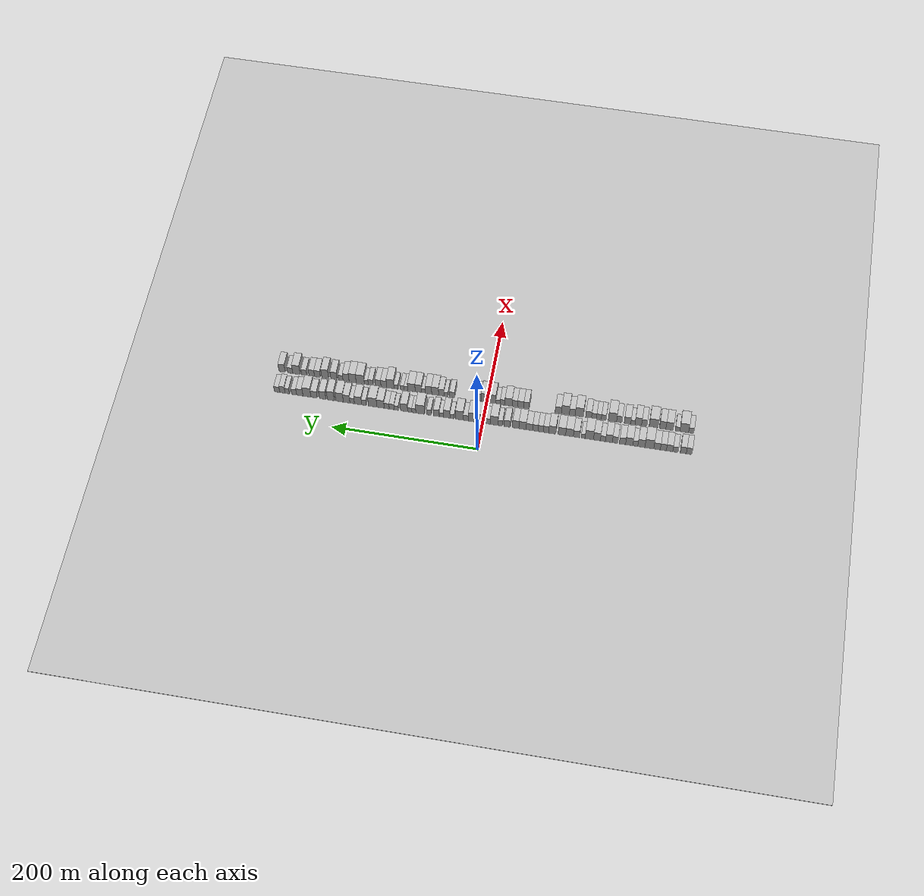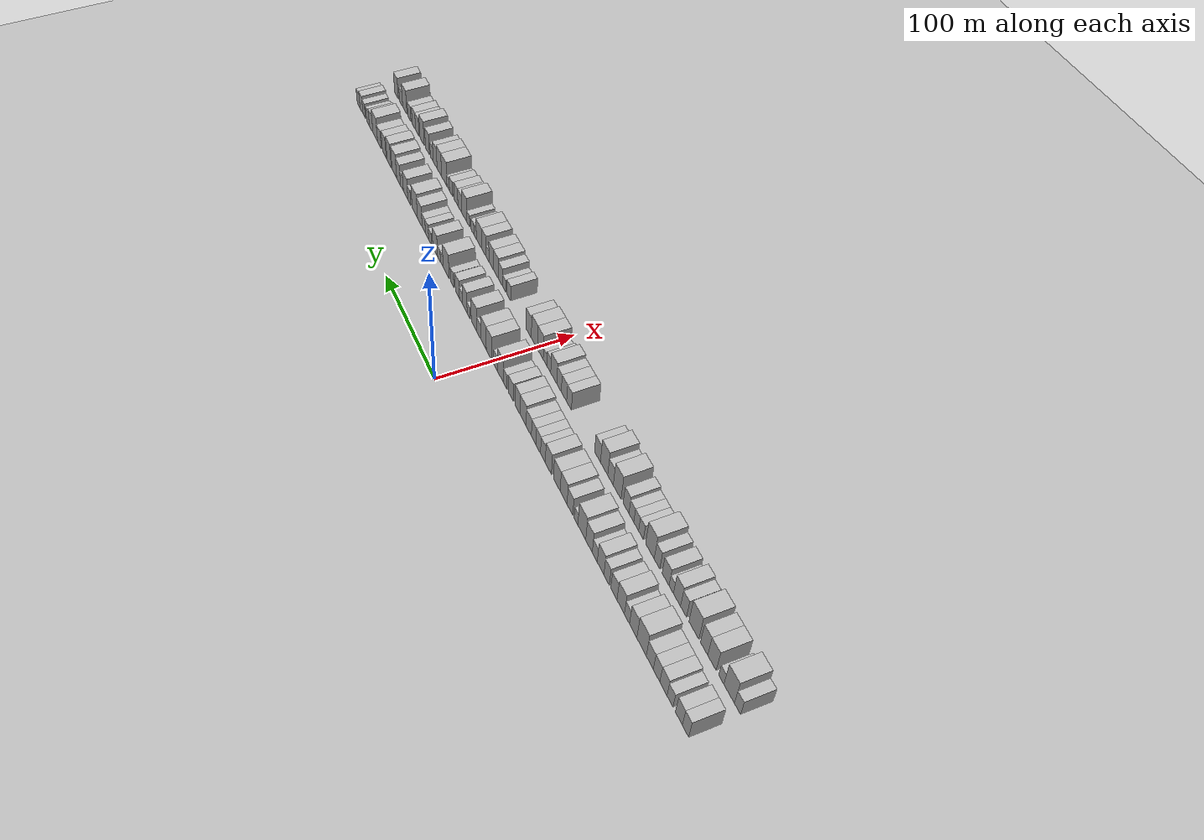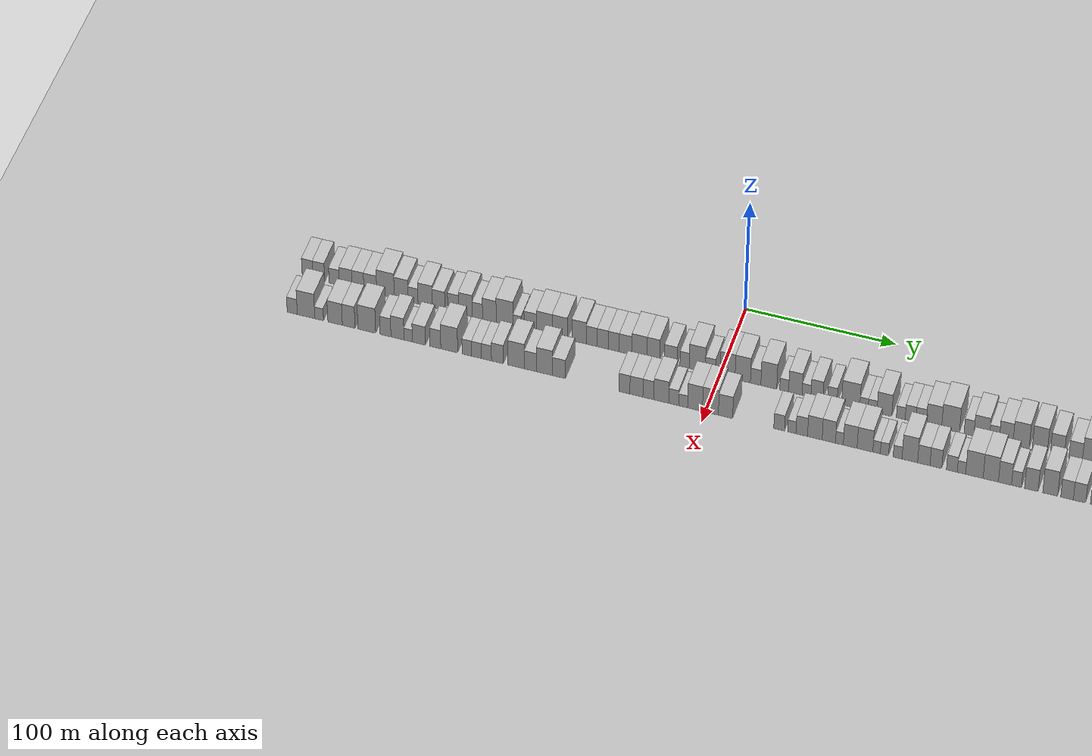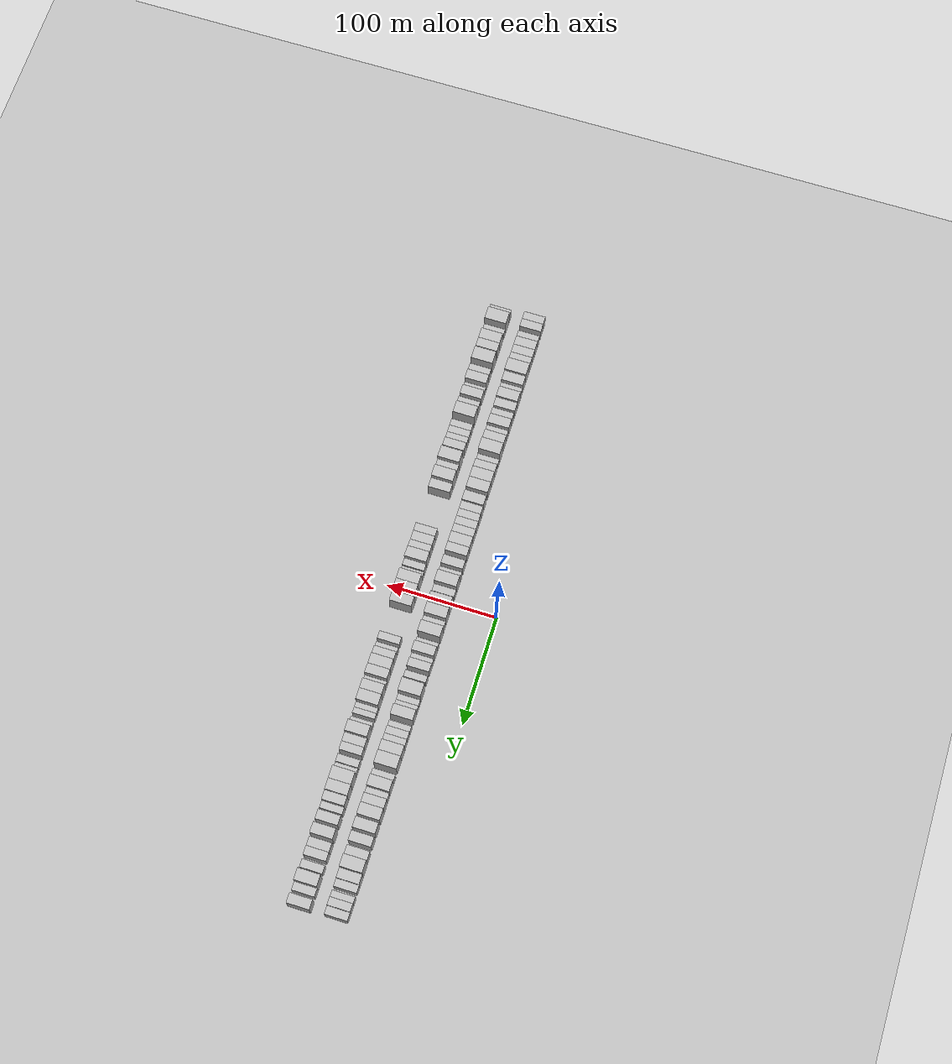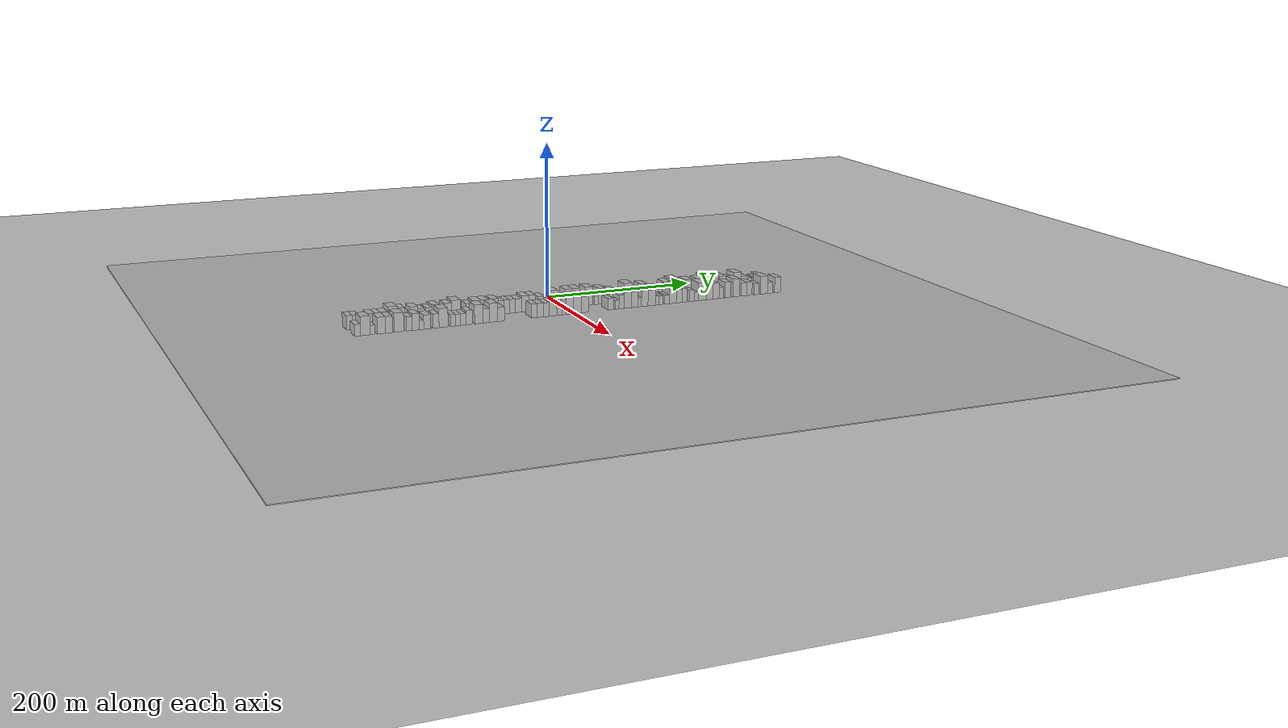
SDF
<?xml version="1.0" encoding="utf-8"?>

<sdf version="1.6">

   <world name="default">

      <gui fullscreen="0">

         <camera name="user_camera">

            <pose>-15 0 4.57585 0 0 0</pose>

            <view_controller>orbit</view_controller>

         </camera>

      </gui>

      <scene>

         <sky>

           <clouds>

             <speed>12</speed>

           </clouds>

         </sky>

         <ambient>0.4 0.4 0.4 1</ambient>

         <background>0.7 0.7 0.7 1</background>

         <shadows>1</shadows>

      </scene>

      <gravity>0 0 -9.8066</gravity>

      <magnetic_field>6e-06 2.3e-05 -4.2e-05</magnetic_field>

      <physics default="0" name="default_physics" type="ode">

         <ode>

            <solver>

               <type>quick</type>

               <iters>10</iters>

               <sor>1.0</sor>

               <use_dynamic_moi_rescaling>0</use_dynamic_moi_rescaling>

            </solver>

            <constraints>

               <cfm>0</cfm>

               <erp>0.2</erp>

               <contact_max_correcting_vel>100</contact_max_correcting_vel>

               <contact_surface_layer>0.001</contact_surface_layer>

            </constraints>

         </ode>

         <max_step_size>0.004</max_step_size>

         <real_time_factor>1</real_time_factor>

         <real_time_update_rate>250</real_time_update_rate>

      </physics>

      <light name="sun" type="directional">

         <cast_shadows>1</cast_shadows>

         <pose>0 0 10 0 0 0</pose>

         <diffuse>0.8 0.8 0.8 1</diffuse>

         <specular>0.2 0.2 0.2 1</specular>

         <attenuation>

            <range>1000</range>

            <constant>0.9</constant>

            <linear>0.01</linear>

            <quadratic>0.001</quadratic>

         </attenuation>

         <direction>-0.5 0.1 -0.9</direction>

      </light>

      <include>

         <name>ground_plane_1</name>

         <uri>model://HANNAS_ground_plane</uri>

         <pose>0 0 0  0 0 0</pose>

      </include>

      <include>

         <name>ground_plane_2</name>

         <uri>model://HANNAS_ground_plane</uri>

         <pose>100 0 0  0 0 0</pose>

      </include>

      <model name="building_1">

         <static>1</static>

         <pose frame="">50.0000 -278.2925 0 0.000000 0.000000 0.000000</pose>

         <link name="link">

            <pose frame="">0 0 9.00 0 0 0</pose>

            <collision name="collision">

               <geometry>

                  <box>

                     <size>20.0000 7.4150 18.0000</size>

                  </box>

               </geometry>

               <max_contacts>10</max_contacts>

               <surface>

                  <contact>

                     <ode/>

                  </contact>

                  <bounce/>

                  <friction>

                     <torsional>

                        <ode/>

                     </torsional>

                     <ode/>

                  </friction>

               </surface>

            </collision>

            <visual name="visual">

               <cast_shadows>0</cast_shadows>

               <geometry>

                  <box>

                     <size>20.0000 7.4150 18.0000</size>

                  </box>

               </geometry>

               <material>

                  <script>

                     <uri>model://HANNAS_wall/materials/scripts</uri>

                     <uri>model://HANNAS_wall/materials/textures</uri>

                     <name>vrc/HANNAS_wall</name>

                  </script>

               </material>

            </visual>

            <self_collide>0</self_collide>

            <enable_wind>0</enable_wind>

            <kinematic>0</kinematic>

         </link>

      </model>

      <model name="building_2">

         <static>1</static>

         <pose frame="">50.0000 -270.5719 0 0.000000 0.000000 0.000000</pose>

         <link name="link">

            <pose frame="">0 0 9.00 0 0 0</pose>

            <collision name="collision">

               <geometry>

                  <box>

                     <size>20.0000 8.0263 18.0000</size>

                  </box>

               </geometry>

               <max_contacts>10</max_contacts>

               <surface>

                  <contact>

                     <ode/>

                  </contact>

                  <bounce/>

                  <friction>

                     <torsional>

                        <ode/>

                     </torsional>

                     <ode/>

                  </friction>

               </surface>

            </collision>

            <visual name="visual">

               <cast_shadows>0</cast_shadows>

               <geometry>

                  <box>

                     <size>20.0000 8.0263 18.0000</size>

                  </box>

               </geometry>

               <material>

                  <script>

                     <uri>model://HANNAS_wall/materials/scripts</uri>

                     <uri>model://HANNAS_wall/materials/textures</uri>

                     <name>vrc/HANNAS_wall</name>

                  </script>

               </material>

            </visual>

            <self_collide>0</self_collide>

            <enable_wind>0</enable_wind>

            <kinematic>0</kinematic>

         </link>

      </model>

      <model name="building_3">

         <static>1</static>

         <pose frame="">50.0000 -260.0088 0 0.000000 0.000000 0.000000</pose>

         <link name="link">

            <pose frame="">0 0 7.50 0 0 0</pose>

            <collision name="collision">

               <geometry>

                  <box>

                     <size>20.0000 7.0998 15.0000</size>

                  </box>

               </geometry>

               <max_contacts>10</max_contacts>

               <surface>

                  <contact>

                     <ode/>

                  </contact>

                  <bounce/>

                  <friction>

                     <torsional>

                        <ode/>

                     </torsional>

                     <ode/>

                  </friction>

               </surface>

            </collision>

            <visual name="visual">

               <cast_shadows>0</cast_shadows>

               <geometry>

                  <box>

                     <size>20.0000 7.0998 15.0000</size>

                  </box>

               </geometry>

               <material>

                  <script>

                     <uri>model://HANNAS_wall/materials/scripts</uri>

                     <uri>model://HANNAS_wall/materials/textures</uri>

                     <name>vrc/HANNAS_wall</name>

                  </script>

               </material>

            </visual>

            <self_collide>0</self_collide>

            <enable_wind>0</enable_wind>

            <kinematic>0</kinematic>

         </link>

      </model>

      <model name="building_4">

         <static>1</static>

         <pose frame="">50.0000 -252.1099 0 0.000000 0.000000 0.000000</pose>

         <link name="link">

            <pose frame="">0 0 9.00 0 0 0</pose>

            <collision name="collision">

               <geometry>

                  <box>

                     <size>20.0000 8.6981 18.0000</size>

                  </box>

               </geometry>

               <max_contacts>10</max_contacts>

               <surface>

                  <contact>

                     <ode/>

                  </contact>

                  <bounce/>

                  <friction>

                     <torsional>

                        <ode/>

                     </torsional>

                     <ode/>

                  </friction>

               </surface>

            </collision>

            <visual name="visual">

               <cast_shadows>0</cast_shadows>

               <geometry>

                  <box>

                     <size>20.0000 8.6981 18.0000</size>

                  </box>

               </geometry>

               <material>

                  <script>

                     <uri>model://HANNAS_wall/materials/scripts</uri>

                     <uri>model://HANNAS_wall/materials/textures</uri>

                     <name>vrc/HANNAS_wall</name>

                  </script>

               </material>

            </visual>

            <self_collide>0</self_collide>

            <enable_wind>0</enable_wind>

            <kinematic>0</kinematic>

         </link>

      </model>

      <model name="building_5">

         <static>1</static>

         <pose frame="">50.0000 -243.7497 0 0.000000 0.000000 0.000000</pose>

         <link name="link">

            <pose frame="">0 0 9.00 0 0 0</pose>

            <collision name="collision">

               <geometry>

                  <box>

                     <size>20.0000 8.0222 18.0000</size>

                  </box>

               </geometry>

               <max_contacts>10</max_contacts>

               <surface>

                  <contact>

                     <ode/>

                  </contact>

                  <bounce/>

                  <friction>

                     <torsional>

                        <ode/>

                     </torsional>

                     <ode/>

                  </friction>

               </surface>

            </collision>

            <visual name="visual">

               <cast_shadows>0</cast_shadows>

               <geometry>

                  <box>

                     <size>20.0000 8.0222 18.0000</size>

                  </box>

               </geometry>

               <material>

                  <script>

                     <uri>model://HANNAS_wall/materials/scripts</uri>

                     <uri>model://HANNAS_wall/materials/textures</uri>

                     <name>vrc/HANNAS_wall</name>

                  </script>

               </material>

            </visual>

            <self_collide>0</self_collide>

            <enable_wind>0</enable_wind>

            <kinematic>0</kinematic>

         </link>

      </model>

      <model name="building_6">

         <static>1</static>

         <pose frame="">50.0000 -235.3451 0 0.000000 0.000000 0.000000</pose>

         <link name="link">

            <pose frame="">0 0 9.00 0 0 0</pose>

            <collision name="collision">

               <geometry>

                  <box>

                     <size>20.0000 8.7870 18.0000</size>

                  </box>

               </geometry>

               <max_contacts>10</max_contacts>

               <surface>

                  <contact>

                     <ode/>

                  </contact>

                  <bounce/>

                  <friction>

                     <torsional>

                        <ode/>

                     </torsional>

                     <ode/>

                  </friction>

               </surface>

            </collision>

            <visual name="visual">

               <cast_shadows>0</cast_shadows>

               <geometry>

                  <box>

                     <size>20.0000 8.7870 18.0000</size>

                  </box>

               </geometry>

               <material>

                  <script>

                     <uri>model://HANNAS_wall/materials/scripts</uri>

                     <uri>model://HANNAS_wall/materials/textures</uri>

                     <name>vrc/HANNAS_wall</name>

                  </script>

               </material>

            </visual>

            <self_collide>0</self_collide>

            <enable_wind>0</enable_wind>

            <kinematic>0</kinematic>

         </link>

      </model>

      <model name="building_7">

         <static>1</static>

         <pose frame="">50.0000 -224.9635 0 0.000000 0.000000 0.000000</pose>

         <link name="link">

            <pose frame="">0 0 12.00 0 0 0</pose>

            <collision name="collision">

               <geometry>

                  <box>

                     <size>20.0000 11.9763 24.0000</size>

                  </box>

               </geometry>

               <max_contacts>10</max_contacts>

               <surface>

                  <contact>

                     <ode/>

                  </contact>

                  <bounce/>

                  <friction>

                     <torsional>

                        <ode/>

                     </torsional>

                     <ode/>

                  </friction>

               </surface>

            </collision>

            <visual name="visual">

               <cast_shadows>0</cast_shadows>

               <geometry>

                  <box>

                     <size>20.0000 11.9763 24.0000</size>

                  </box>

               </geometry>

               <material>

                  <script>

                     <uri>model://HANNAS_wall/materials/scripts</uri>

                     <uri>model://HANNAS_wall/materials/textures</uri>

                     <name>vrc/HANNAS_wall</name>

                  </script>

               </material>

            </visual>

            <self_collide>0</self_collide>

            <enable_wind>0</enable_wind>

            <kinematic>0</kinematic>

         </link>

      </model>

      <model name="building_8">

         <static>1</static>

         <pose frame="">50.0000 -214.2349 0 0.000000 0.000000 0.000000</pose>

         <link name="link">

            <pose frame="">0 0 10.50 0 0 0</pose>

            <collision name="collision">

               <geometry>

                  <box>

                     <size>20.0000 9.4808 21.0000</size>

                  </box>

               </geometry>

               <max_contacts>10</max_contacts>

               <surface>

                  <contact>

                     <ode/>

                  </contact>

                  <bounce/>

                  <friction>

                     <torsional>

                        <ode/>

                     </torsional>

                     <ode/>

                  </friction>

               </surface>

            </collision>

            <visual name="visual">

               <cast_shadows>0</cast_shadows>

               <geometry>

                  <box>

                     <size>20.0000 9.4808 21.0000</size>

                  </box>

               </geometry>

               <material>

                  <script>

                     <uri>model://HANNAS_wall/materials/scripts</uri>

                     <uri>model://HANNAS_wall/materials/textures</uri>

                     <name>vrc/HANNAS_wall</name>

                  </script>

               </material>

            </visual>

            <self_collide>0</self_collide>

            <enable_wind>0</enable_wind>

            <kinematic>0</kinematic>

         </link>

      </model>

      <model name="building_9">

         <static>1</static>

         <pose frame="">50.0000 -206.1634 0 0.000000 0.000000 0.000000</pose>

         <link name="link">

            <pose frame="">0 0 7.50 0 0 0</pose>

            <collision name="collision">

               <geometry>

                  <box>

                     <size>20.0000 6.6623 15.0000</size>

                  </box>

               </geometry>

               <max_contacts>10</max_contacts>

               <surface>

                  <contact>

                     <ode/>

                  </contact>

                  <bounce/>

                  <friction>

                     <torsional>

                        <ode/>

                     </torsional>

                     <ode/>

                  </friction>

               </surface>

            </collision>

            <visual name="visual">

               <cast_shadows>0</cast_shadows>

               <geometry>

                  <box>

                     <size>20.0000 6.6623 15.0000</size>

                  </box>

               </geometry>

               <material>

                  <script>

                     <uri>model://HANNAS_wall/materials/scripts</uri>

                     <uri>model://HANNAS_wall/materials/textures</uri>

                     <name>vrc/HANNAS_wall</name>

                  </script>

               </material>

            </visual>

            <self_collide>0</self_collide>

            <enable_wind>0</enable_wind>

            <kinematic>0</kinematic>

         </link>

      </model>

      <model name="building_10">

         <static>1</static>

         <pose frame="">50.0000 -197.9297 0 0.000000 0.000000 0.000000</pose>

         <link name="link">

            <pose frame="">0 0 10.50 0 0 0</pose>

            <collision name="collision">

               <geometry>

                  <box>

                     <size>20.0000 9.8050 21.0000</size>

                  </box>

               </geometry>

               <max_contacts>10</max_contacts>

               <surface>

                  <contact>

                     <ode/>

                  </contact>

                  <bounce/>

                  <friction>

                     <torsional>

                        <ode/>

                     </torsional>

                     <ode/>

                  </friction>

               </surface>

            </collision>

            <visual name="visual">

               <cast_shadows>0</cast_shadows>

               <geometry>

                  <box>

                     <size>20.0000 9.8050 21.0000</size>

                  </box>

               </geometry>

               <material>

                  <script>

                     <uri>model://HANNAS_wall/materials/scripts</uri>

                     <uri>model://HANNAS_wall/materials/textures</uri>

                     <name>vrc/HANNAS_wall</name>

                  </script>

               </material>

            </visual>

            <self_collide>0</self_collide>

            <enable_wind>0</enable_wind>

            <kinematic>0</kinematic>

         </link>

      </model>

      <model name="building_11">

         <static>1</static>

         <pose frame="">50.0000 -188.8027 0 0.000000 0.000000 0.000000</pose>

         <link name="link">

            <pose frame="">0 0 9.00 0 0 0</pose>

            <collision name="collision">

               <geometry>

                  <box>

                     <size>20.0000 8.4491 18.0000</size>

                  </box>

               </geometry>

               <max_contacts>10</max_contacts>

               <surface>

                  <contact>

                     <ode/>

                  </contact>

                  <bounce/>

                  <friction>

                     <torsional>

                        <ode/>

                     </torsional>

                     <ode/>

                  </friction>

               </surface>

            </collision>

            <visual name="visual">

               <cast_shadows>0</cast_shadows>

               <geometry>

                  <box>

                     <size>20.0000 8.4491 18.0000</size>

                  </box>

               </geometry>

               <material>

                  <script>

                     <uri>model://HANNAS_wall/materials/scripts</uri>

                     <uri>model://HANNAS_wall/materials/textures</uri>

                     <name>vrc/HANNAS_wall</name>

                  </script>

               </material>

            </visual>

            <self_collide>0</self_collide>

            <enable_wind>0</enable_wind>

            <kinematic>0</kinematic>

         </link>

      </model>

      <model name="building_12">

         <static>1</static>

         <pose frame="">50.0000 -178.9044 0 0.000000 0.000000 0.000000</pose>

         <link name="link">

            <pose frame="">0 0 9.00 0 0 0</pose>

            <collision name="collision">

               <geometry>

                  <box>

                     <size>20.0000 7.3475 18.0000</size>

                  </box>

               </geometry>

               <max_contacts>10</max_contacts>

               <surface>

                  <contact>

                     <ode/>

                  </contact>

                  <bounce/>

                  <friction>

                     <torsional>

                        <ode/>

                     </torsional>

                     <ode/>

                  </friction>

               </surface>

            </collision>

            <visual name="visual">

               <cast_shadows>0</cast_shadows>

               <geometry>

                  <box>

                     <size>20.0000 7.3475 18.0000</size>

                  </box>

               </geometry>

               <material>

                  <script>

                     <uri>model://HANNAS_wall/materials/scripts</uri>

                     <uri>model://HANNAS_wall/materials/textures</uri>

                     <name>vrc/HANNAS_wall</name>

                  </script>

               </material>

            </visual>

            <self_collide>0</self_collide>

            <enable_wind>0</enable_wind>

            <kinematic>0</kinematic>

         </link>

      </model>

      <model name="building_13">

         <static>1</static>

         <pose frame="">50.0000 -170.6135 0 0.000000 0.000000 0.000000</pose>

         <link name="link">

            <pose frame="">0 0 10.50 0 0 0</pose>

            <collision name="collision">

               <geometry>

                  <box>

                     <size>20.0000 9.2345 21.0000</size>

                  </box>

               </geometry>

               <max_contacts>10</max_contacts>

               <surface>

                  <contact>

                     <ode/>

                  </contact>

                  <bounce/>

                  <friction>

                     <torsional>

                        <ode/>

                     </torsional>

                     <ode/>

                  </friction>

               </surface>

            </collision>

            <visual name="visual">

               <cast_shadows>0</cast_shadows>

               <geometry>

                  <box>

                     <size>20.0000 9.2345 21.0000</size>

                  </box>

               </geometry>

               <material>

                  <script>

                     <uri>model://HANNAS_wall/materials/scripts</uri>

                     <uri>model://HANNAS_wall/materials/textures</uri>

                     <name>vrc/HANNAS_wall</name>

                  </script>

               </material>

            </visual>

            <self_collide>0</self_collide>

            <enable_wind>0</enable_wind>

            <kinematic>0</kinematic>

         </link>

      </model>

      <model name="building_14">

         <static>1</static>

         <pose frame="">50.0000 -162.5183 0 0.000000 0.000000 0.000000</pose>

         <link name="link">

            <pose frame="">0 0 7.50 0 0 0</pose>

            <collision name="collision">

               <geometry>

                  <box>

                     <size>20.0000 6.9559 15.0000</size>

                  </box>

               </geometry>

               <max_contacts>10</max_contacts>

               <surface>

                  <contact>

                     <ode/>

                  </contact>

                  <bounce/>

                  <friction>

                     <torsional>

                        <ode/>

                     </torsional>

                     <ode/>

                  </friction>

               </surface>

            </collision>

            <visual name="visual">

               <cast_shadows>0</cast_shadows>

               <geometry>

                  <box>

                     <size>20.0000 6.9559 15.0000</size>

                  </box>

               </geometry>

               <material>

                  <script>

                     <uri>model://HANNAS_wall/materials/scripts</uri>

                     <uri>model://HANNAS_wall/materials/textures</uri>

                     <name>vrc/HANNAS_wall</name>

                  </script>

               </material>

            </visual>

            <self_collide>0</self_collide>

            <enable_wind>0</enable_wind>

            <kinematic>0</kinematic>

         </link>

      </model>

      <model name="building_15">

         <static>1</static>

         <pose frame="">50.0000 -154.4109 0 0.000000 0.000000 0.000000</pose>

         <link name="link">

            <pose frame="">0 0 10.50 0 0 0</pose>

            <collision name="collision">

               <geometry>

                  <box>

                     <size>20.0000 9.2589 21.0000</size>

                  </box>

               </geometry>

               <max_contacts>10</max_contacts>

               <surface>

                  <contact>

                     <ode/>

                  </contact>

                  <bounce/>

                  <friction>

                     <torsional>

                        <ode/>

                     </torsional>

                     <ode/>

                  </friction>

               </surface>

            </collision>

            <visual name="visual">

               <cast_shadows>0</cast_shadows>

               <geometry>

                  <box>

                     <size>20.0000 9.2589 21.0000</size>

                  </box>

               </geometry>

               <material>

                  <script>

                     <uri>model://HANNAS_wall/materials/scripts</uri>

                     <uri>model://HANNAS_wall/materials/textures</uri>

                     <name>vrc/HANNAS_wall</name>

                  </script>

               </material>

            </visual>

            <self_collide>0</self_collide>

            <enable_wind>0</enable_wind>

            <kinematic>0</kinematic>

         </link>

      </model>

      <model name="building_16">

         <static>1</static>

         <pose frame="">50.0000 -144.0825 0 0.000000 0.000000 0.000000</pose>

         <link name="link">

            <pose frame="">0 0 12.00 0 0 0</pose>

            <collision name="collision">

               <geometry>

                  <box>

                     <size>20.0000 11.3979 24.0000</size>

                  </box>

               </geometry>

               <max_contacts>10</max_contacts>

               <surface>

                  <contact>

                     <ode/>

                  </contact>

                  <bounce/>

                  <friction>

                     <torsional>

                        <ode/>

                     </torsional>

                     <ode/>

                  </friction>

               </surface>

            </collision>

            <visual name="visual">

               <cast_shadows>0</cast_shadows>

               <geometry>

                  <box>

                     <size>20.0000 11.3979 24.0000</size>

                  </box>

               </geometry>

               <material>

                  <script>

                     <uri>model://HANNAS_wall/materials/scripts</uri>

                     <uri>model://HANNAS_wall/materials/textures</uri>

                     <name>vrc/HANNAS_wall</name>

                  </script>

               </material>

            </visual>

            <self_collide>0</self_collide>

            <enable_wind>0</enable_wind>

            <kinematic>0</kinematic>

         </link>

      </model>

      <model name="building_17">

         <static>1</static>

         <pose frame="">50.0000 -135.6626 0 0.000000 0.000000 0.000000</pose>

         <link name="link">

            <pose frame="">0 0 6.00 0 0 0</pose>

            <collision name="collision">

               <geometry>

                  <box>

                     <size>20.0000 5.4421 12.0000</size>

                  </box>

               </geometry>

               <max_contacts>10</max_contacts>

               <surface>

                  <contact>

                     <ode/>

                  </contact>

                  <bounce/>

                  <friction>

                     <torsional>

                        <ode/>

                     </torsional>

                     <ode/>

                  </friction>

               </surface>

            </collision>

            <visual name="visual">

               <cast_shadows>0</cast_shadows>

               <geometry>

                  <box>

                     <size>20.0000 5.4421 12.0000</size>

                  </box>

               </geometry>

               <material>

                  <script>

                     <uri>model://HANNAS_wall/materials/scripts</uri>

                     <uri>model://HANNAS_wall/materials/textures</uri>

                     <name>vrc/HANNAS_wall</name>

                  </script>

               </material>

            </visual>

            <self_collide>0</self_collide>

            <enable_wind>0</enable_wind>

            <kinematic>0</kinematic>

         </link>

      </model>

      <model name="building_18">

         <static>1</static>

         <pose frame="">50.0000 -126.6922 0 0.000000 0.000000 0.000000</pose>

         <link name="link">

            <pose frame="">0 0 9.00 0 0 0</pose>

            <collision name="collision">

               <geometry>

                  <box>

                     <size>20.0000 8.4987 18.0000</size>

                  </box>

               </geometry>

               <max_contacts>10</max_contacts>

               <surface>

                  <contact>

                     <ode/>

                  </contact>

                  <bounce/>

                  <friction>

                     <torsional>

                        <ode/>

                     </torsional>

                     <ode/>

                  </friction>

               </surface>

            </collision>

            <visual name="visual">

               <cast_shadows>0</cast_shadows>

               <geometry>

                  <box>

                     <size>20.0000 8.4987 18.0000</size>

                  </box>

               </geometry>

               <material>

                  <script>

                     <uri>model://HANNAS_wall/materials/scripts</uri>

                     <uri>model://HANNAS_wall/materials/textures</uri>

                     <name>vrc/HANNAS_wall</name>

                  </script>

               </material>

            </visual>

            <self_collide>0</self_collide>

            <enable_wind>0</enable_wind>

            <kinematic>0</kinematic>

         </link>

      </model>

      <model name="building_19">

         <static>1</static>

         <pose frame="">50.0000 -117.2545 0 0.000000 0.000000 0.000000</pose>

         <link name="link">

            <pose frame="">0 0 10.50 0 0 0</pose>

            <collision name="collision">

               <geometry>

                  <box>

                     <size>20.0000 10.3768 21.0000</size>

                  </box>

               </geometry>

               <max_contacts>10</max_contacts>

               <surface>

                  <contact>

                     <ode/>

                  </contact>

                  <bounce/>

                  <friction>

                     <torsional>

                        <ode/>

                     </torsional>

                     <ode/>

                  </friction>

               </surface>

            </collision>

            <visual name="visual">

               <cast_shadows>0</cast_shadows>

               <geometry>

                  <box>

                     <size>20.0000 10.3768 21.0000</size>

                  </box>

               </geometry>

               <material>

                  <script>

                     <uri>model://HANNAS_wall/materials/scripts</uri>

                     <uri>model://HANNAS_wall/materials/textures</uri>

                     <name>vrc/HANNAS_wall</name>

                  </script>

               </material>

            </visual>

            <self_collide>0</self_collide>

            <enable_wind>0</enable_wind>

            <kinematic>0</kinematic>

         </link>

      </model>

      <model name="building_20">

         <static>1</static>

         <pose frame="">50.0000 -106.9224 0 0.000000 0.000000 0.000000</pose>

         <link name="link">

            <pose frame="">0 0 10.50 0 0 0</pose>

            <collision name="collision">

               <geometry>

                  <box>

                     <size>20.0000 10.2875 21.0000</size>

                  </box>

               </geometry>

               <max_contacts>10</max_contacts>

               <surface>

                  <contact>

                     <ode/>

                  </contact>

                  <bounce/>

                  <friction>

                     <torsional>

                        <ode/>

                     </torsional>

                     <ode/>

                  </friction>

               </surface>

            </collision>

            <visual name="visual">

               <cast_shadows>0</cast_shadows>

               <geometry>

                  <box>

                     <size>20.0000 10.2875 21.0000</size>

                  </box>

               </geometry>

               <material>

                  <script>

                     <uri>model://HANNAS_wall/materials/scripts</uri>

                     <uri>model://HANNAS_wall/materials/textures</uri>

                     <name>vrc/HANNAS_wall</name>

                  </script>

               </material>

            </visual>

            <self_collide>0</self_collide>

            <enable_wind>0</enable_wind>

            <kinematic>0</kinematic>

         </link>

      </model>

      <model name="building_21">

         <static>1</static>

         <pose frame="">50.0000 -93.9929 0 0.000000 0.000000 0.000000</pose>

         <link name="link">

            <pose frame="">0 0 10.50 0 0 0</pose>

            <collision name="collision">

               <geometry>

                  <box>

                     <size>20.0000 9.5714 21.0000</size>

                  </box>

               </geometry>

               <max_contacts>10</max_contacts>

               <surface>

                  <contact>

                     <ode/>

                  </contact>

                  <bounce/>

                  <friction>

                     <torsional>

                        <ode/>

                     </torsional>

                     <ode/>

                  </friction>

               </surface>

            </collision>

            <visual name="visual">

               <cast_shadows>0</cast_shadows>

               <geometry>

                  <box>

                     <size>20.0000 9.5714 21.0000</size>

                  </box>

               </geometry>

               <material>

                  <script>

                     <uri>model://HANNAS_wall/materials/scripts</uri>

                     <uri>model://HANNAS_wall/materials/textures</uri>

                     <name>vrc/HANNAS_wall</name>

                  </script>

               </material>

            </visual>

            <self_collide>0</self_collide>

            <enable_wind>0</enable_wind>

            <kinematic>0</kinematic>

         </link>

      </model>

      <model name="building_22">

         <static>1</static>

         <pose frame="">50.0000 -85.4480 0 0.000000 0.000000 0.000000</pose>

         <link name="link">

            <pose frame="">0 0 9.00 0 0 0</pose>

            <collision name="collision">

               <geometry>

                  <box>

                     <size>20.0000 7.5185 18.0000</size>

                  </box>

               </geometry>

               <max_contacts>10</max_contacts>

               <surface>

                  <contact>

                     <ode/>

                  </contact>

                  <bounce/>

                  <friction>

                     <torsional>

                        <ode/>

                     </torsional>

                     <ode/>

                  </friction>

               </surface>

            </collision>

            <visual name="visual">

               <cast_shadows>0</cast_shadows>

               <geometry>

                  <box>

                     <size>20.0000 7.5185 18.0000</size>

                  </box>

               </geometry>

               <material>

                  <script>

                     <uri>model://HANNAS_wall/materials/scripts</uri>

                     <uri>model://HANNAS_wall/materials/textures</uri>

                     <name>vrc/HANNAS_wall</name>

                  </script>

               </material>

            </visual>

            <self_collide>0</self_collide>

            <enable_wind>0</enable_wind>

            <kinematic>0</kinematic>

         </link>

      </model>

      <model name="building_23">

         <static>1</static>

         <pose frame="">50.0000 -78.0797 0 0.000000 0.000000 0.000000</pose>

         <link name="link">

            <pose frame="">0 0 9.00 0 0 0</pose>

            <collision name="collision">

               <geometry>

                  <box>

                     <size>20.0000 7.2181 18.0000</size>

                  </box>

               </geometry>

               <max_contacts>10</max_contacts>

               <surface>

                  <contact>

                     <ode/>

                  </contact>

                  <bounce/>

                  <friction>

                     <torsional>

                        <ode/>

                     </torsional>

                     <ode/>

                  </friction>

               </surface>

            </collision>

            <visual name="visual">

               <cast_shadows>0</cast_shadows>

               <geometry>

                  <box>

                     <size>20.0000 7.2181 18.0000</size>

                  </box>

               </geometry>

               <material>

                  <script>

                     <uri>model://HANNAS_wall/materials/scripts</uri>

                     <uri>model://HANNAS_wall/materials/textures</uri>

                     <name>vrc/HANNAS_wall</name>

                  </script>

               </material>

            </visual>

            <self_collide>0</self_collide>

            <enable_wind>0</enable_wind>

            <kinematic>0</kinematic>

         </link>

      </model>

      <model name="building_24">

         <static>1</static>

         <pose frame="">50.0000 -70.7498 0 0.000000 0.000000 0.000000</pose>

         <link name="link">

            <pose frame="">0 0 9.00 0 0 0</pose>

            <collision name="collision">

               <geometry>

                  <box>

                     <size>20.0000 7.4417 18.0000</size>

                  </box>

               </geometry>

               <max_contacts>10</max_contacts>

               <surface>

                  <contact>

                     <ode/>

                  </contact>

                  <bounce/>

                  <friction>

                     <torsional>

                        <ode/>

                     </torsional>

                     <ode/>

                  </friction>

               </surface>

            </collision>

            <visual name="visual">

               <cast_shadows>0</cast_shadows>

               <geometry>

                  <box>

                     <size>20.0000 7.4417 18.0000</size>

                  </box>

               </geometry>

               <material>

                  <script>

                     <uri>model://HANNAS_wall/materials/scripts</uri>

                     <uri>model://HANNAS_wall/materials/textures</uri>

                     <name>vrc/HANNAS_wall</name>

                  </script>

               </material>

            </visual>

            <self_collide>0</self_collide>

            <enable_wind>0</enable_wind>

            <kinematic>0</kinematic>

         </link>

      </model>

      <model name="building_25">

         <static>1</static>

         <pose frame="">50.0000 -62.7737 0 0.000000 0.000000 0.000000</pose>

         <link name="link">

            <pose frame="">0 0 9.00 0 0 0</pose>

            <collision name="collision">

               <geometry>

                  <box>

                     <size>20.0000 8.5106 18.0000</size>

                  </box>

               </geometry>

               <max_contacts>10</max_contacts>

               <surface>

                  <contact>

                     <ode/>

                  </contact>

                  <bounce/>

                  <friction>

                     <torsional>

                        <ode/>

                     </torsional>

                     <ode/>

                  </friction>

               </surface>

            </collision>

            <visual name="visual">

               <cast_shadows>0</cast_shadows>

               <geometry>

                  <box>

                     <size>20.0000 8.5106 18.0000</size>

                  </box>

               </geometry>

               <material>

                  <script>

                     <uri>model://HANNAS_wall/materials/scripts</uri>

                     <uri>model://HANNAS_wall/materials/textures</uri>

                     <name>vrc/HANNAS_wall</name>

                  </script>

               </material>

            </visual>

            <self_collide>0</self_collide>

            <enable_wind>0</enable_wind>

            <kinematic>0</kinematic>

         </link>

      </model>

      <model name="building_26">

         <static>1</static>

         <pose frame="">50.0000 -53.4674 0 0.000000 0.000000 0.000000</pose>

         <link name="link">

            <pose frame="">0 0 10.50 0 0 0</pose>

            <collision name="collision">

               <geometry>

                  <box>

                     <size>20.0000 10.1021 21.0000</size>

                  </box>

               </geometry>

               <max_contacts>10</max_contacts>

               <surface>

                  <contact>

                     <ode/>

                  </contact>

                  <bounce/>

                  <friction>

                     <torsional>

                        <ode/>

                     </torsional>

                     <ode/>

                  </friction>

               </surface>

            </collision>

            <visual name="visual">

               <cast_shadows>0</cast_shadows>

               <geometry>

                  <box>

                     <size>20.0000 10.1021 21.0000</size>

                  </box>

               </geometry>

               <material>

                  <script>

                     <uri>model://HANNAS_wall/materials/scripts</uri>

                     <uri>model://HANNAS_wall/materials/textures</uri>

                     <name>vrc/HANNAS_wall</name>

                  </script>

               </material>

            </visual>

            <self_collide>0</self_collide>

            <enable_wind>0</enable_wind>

            <kinematic>0</kinematic>

         </link>

      </model>

      <model name="building_27">

         <static>1</static>

         <pose frame="">50.0000 -44.1597 0 0.000000 0.000000 0.000000</pose>

         <link name="link">

            <pose frame="">0 0 10.50 0 0 0</pose>

            <collision name="collision">

               <geometry>

                  <box>

                     <size>20.0000 8.5132 21.0000</size>

                  </box>

               </geometry>

               <max_contacts>10</max_contacts>

               <surface>

                  <contact>

                     <ode/>

                  </contact>

                  <bounce/>

                  <friction>

                     <torsional>

                        <ode/>

                     </torsional>

                     <ode/>

                  </friction>

               </surface>

            </collision>

            <visual name="visual">

               <cast_shadows>0</cast_shadows>

               <geometry>

                  <box>

                     <size>20.0000 8.5132 21.0000</size>

                  </box>

               </geometry>

               <material>

                  <script>

                     <uri>model://HANNAS_wall/materials/scripts</uri>

                     <uri>model://HANNAS_wall/materials/textures</uri>

                     <name>vrc/HANNAS_wall</name>

                  </script>

               </material>

            </visual>

            <self_collide>0</self_collide>

            <enable_wind>0</enable_wind>

            <kinematic>0</kinematic>

         </link>

      </model>

      <model name="building_28">

         <static>1</static>

         <pose frame="">50.0000 -32.6811 0 0.000000 0.000000 0.000000</pose>

         <link name="link">

            <pose frame="">0 0 9.00 0 0 0</pose>

            <collision name="collision">

               <geometry>

                  <box>

                     <size>20.0000 8.4440 18.0000</size>

                  </box>

               </geometry>

               <max_contacts>10</max_contacts>

               <surface>

                  <contact>

                     <ode/>

                  </contact>

                  <bounce/>

                  <friction>

                     <torsional>

                        <ode/>

                     </torsional>

                     <ode/>

                  </friction>

               </surface>

            </collision>

            <visual name="visual">

               <cast_shadows>0</cast_shadows>

               <geometry>

                  <box>

                     <size>20.0000 8.4440 18.0000</size>

                  </box>

               </geometry>

               <material>

                  <script>

                     <uri>model://HANNAS_wall/materials/scripts</uri>

                     <uri>model://HANNAS_wall/materials/textures</uri>

                     <name>vrc/HANNAS_wall</name>

                  </script>

               </material>

            </visual>

            <self_collide>0</self_collide>

            <enable_wind>0</enable_wind>

            <kinematic>0</kinematic>

         </link>

      </model>

      <model name="building_29">

         <static>1</static>

         <pose frame="">50.0000 -23.3607 0 0.000000 0.000000 0.000000</pose>

         <link name="link">

            <pose frame="">0 0 7.50 0 0 0</pose>

            <collision name="collision">

               <geometry>

                  <box>

                     <size>20.0000 6.1967 15.0000</size>

                  </box>

               </geometry>

               <max_contacts>10</max_contacts>

               <surface>

                  <contact>

                     <ode/>

                  </contact>

                  <bounce/>

                  <friction>

                     <torsional>

                        <ode/>

                     </torsional>

                     <ode/>

                  </friction>

               </surface>

            </collision>

            <visual name="visual">

               <cast_shadows>0</cast_shadows>

               <geometry>

                  <box>

                     <size>20.0000 6.1967 15.0000</size>

                  </box>

               </geometry>

               <material>

                  <script>

                     <uri>model://HANNAS_wall/materials/scripts</uri>

                     <uri>model://HANNAS_wall/materials/textures</uri>

                     <name>vrc/HANNAS_wall</name>

                  </script>

               </material>

            </visual>

            <self_collide>0</self_collide>

            <enable_wind>0</enable_wind>

            <kinematic>0</kinematic>

         </link>

      </model>

      <model name="building_30">

         <static>1</static>

         <pose frame="">50.0000 -14.9194 0 0.000000 0.000000 0.000000</pose>

         <link name="link">

            <pose frame="">0 0 12.00 0 0 0</pose>

            <collision name="collision">

               <geometry>

                  <box>

                     <size>20.0000 10.6859 24.0000</size>

                  </box>

               </geometry>

               <max_contacts>10</max_contacts>

               <surface>

                  <contact>

                     <ode/>

                  </contact>

                  <bounce/>

                  <friction>

                     <torsional>

                        <ode/>

                     </torsional>

                     <ode/>

                  </friction>

               </surface>

            </collision>

            <visual name="visual">

               <cast_shadows>0</cast_shadows>

               <geometry>

                  <box>

                     <size>20.0000 10.6859 24.0000</size>

                  </box>

               </geometry>

               <material>

                  <script>

                     <uri>model://HANNAS_wall/materials/scripts</uri>

                     <uri>model://HANNAS_wall/materials/textures</uri>

                     <name>vrc/HANNAS_wall</name>

                  </script>

               </material>

            </visual>

            <self_collide>0</self_collide>

            <enable_wind>0</enable_wind>

            <kinematic>0</kinematic>

         </link>

      </model>

      <model name="building_31">

         <static>1</static>

         <pose frame="">50.0000 -6.2093 0 0.000000 0.000000 0.000000</pose>

         <link name="link">

            <pose frame="">0 0 7.50 0 0 0</pose>

            <collision name="collision">

               <geometry>

                  <box>

                     <size>20.0000 6.7343 15.0000</size>

                  </box>

               </geometry>

               <max_contacts>10</max_contacts>

               <surface>

                  <contact>

                     <ode/>

                  </contact>

                  <bounce/>

                  <friction>

                     <torsional>

                        <ode/>

                     </torsional>

                     <ode/>

                  </friction>

               </surface>

            </collision>

            <visual name="visual">

               <cast_shadows>0</cast_shadows>

               <geometry>

                  <box>

                     <size>20.0000 6.7343 15.0000</size>

                  </box>

               </geometry>

               <material>

                  <script>

                     <uri>model://HANNAS_wall/materials/scripts</uri>

                     <uri>model://HANNAS_wall/materials/textures</uri>

                     <name>vrc/HANNAS_wall</name>

                  </script>

               </material>

            </visual>

            <self_collide>0</self_collide>

            <enable_wind>0</enable_wind>

            <kinematic>0</kinematic>

         </link>

      </model>

      <model name="building_32">

         <static>1</static>

         <pose frame="">50.0000 5.1715 0 0.000000 0.000000 0.000000</pose>

         <link name="link">

            <pose frame="">0 0 12.00 0 0 0</pose>

            <collision name="collision">

               <geometry>

                  <box>

                     <size>20.0000 10.0273 24.0000</size>

                  </box>

               </geometry>

               <max_contacts>10</max_contacts>

               <surface>

                  <contact>

                     <ode/>

                  </contact>

                  <bounce/>

                  <friction>

                     <torsional>

                        <ode/>

                     </torsional>

                     <ode/>

                  </friction>

               </surface>

            </collision>

            <visual name="visual">

               <cast_shadows>0</cast_shadows>

               <geometry>

                  <box>

                     <size>20.0000 10.0273 24.0000</size>

                  </box>

               </geometry>

               <material>

                  <script>

                     <uri>model://HANNAS_wall/materials/scripts</uri>

                     <uri>model://HANNAS_wall/materials/textures</uri>

                     <name>vrc/HANNAS_wall</name>

                  </script>

               </material>

            </visual>

            <self_collide>0</self_collide>

            <enable_wind>0</enable_wind>

            <kinematic>0</kinematic>

         </link>

      </model>

      <model name="building_33">

         <static>1</static>

         <pose frame="">50.0000 15.2766 0 0.000000 0.000000 0.000000</pose>

         <link name="link">

            <pose frame="">0 0 12.00 0 0 0</pose>

            <collision name="collision">

               <geometry>

                  <box>

                     <size>20.0000 10.1828 24.0000</size>

                  </box>

               </geometry>

               <max_contacts>10</max_contacts>

               <surface>

                  <contact>

                     <ode/>

                  </contact>

                  <bounce/>

                  <friction>

                     <torsional>

                        <ode/>

                     </torsional>

                     <ode/>

                  </friction>

               </surface>

            </collision>

            <visual name="visual">

               <cast_shadows>0</cast_shadows>

               <geometry>

                  <box>

                     <size>20.0000 10.1828 24.0000</size>

                  </box>

               </geometry>

               <material>

                  <script>

                     <uri>model://HANNAS_wall/materials/scripts</uri>

                     <uri>model://HANNAS_wall/materials/textures</uri>

                     <name>vrc/HANNAS_wall</name>

                  </script>

               </material>

            </visual>

            <self_collide>0</self_collide>

            <enable_wind>0</enable_wind>

            <kinematic>0</kinematic>

         </link>

      </model>

      <model name="building_34">

         <static>1</static>

         <pose frame="">50.0000 23.8390 0 0.000000 0.000000 0.000000</pose>

         <link name="link">

            <pose frame="">0 0 7.50 0 0 0</pose>

            <collision name="collision">

               <geometry>

                  <box>

                     <size>20.0000 6.9421 15.0000</size>

                  </box>

               </geometry>

               <max_contacts>10</max_contacts>

               <surface>

                  <contact>

                     <ode/>

                  </contact>

                  <bounce/>

                  <friction>

                     <torsional>

                        <ode/>

                     </torsional>

                     <ode/>

                  </friction>

               </surface>

            </collision>

            <visual name="visual">

               <cast_shadows>0</cast_shadows>

               <geometry>

                  <box>

                     <size>20.0000 6.9421 15.0000</size>

                  </box>

               </geometry>

               <material>

                  <script>

                     <uri>model://HANNAS_wall/materials/scripts</uri>

                     <uri>model://HANNAS_wall/materials/textures</uri>

                     <name>vrc/HANNAS_wall</name>

                  </script>

               </material>

            </visual>

            <self_collide>0</self_collide>

            <enable_wind>0</enable_wind>

            <kinematic>0</kinematic>

         </link>

      </model>

      <model name="building_35">

         <static>1</static>

         <pose frame="">50.0000 32.5696 0 0.000000 0.000000 0.000000</pose>

         <link name="link">

            <pose frame="">0 0 12.00 0 0 0</pose>

            <collision name="collision">

               <geometry>

                  <box>

                     <size>20.0000 10.5189 24.0000</size>

                  </box>

               </geometry>

               <max_contacts>10</max_contacts>

               <surface>

                  <contact>

                     <ode/>

                  </contact>

                  <bounce/>

                  <friction>

                     <torsional>

                        <ode/>

                     </torsional>

                     <ode/>

                  </friction>

               </surface>

            </collision>

            <visual name="visual">

               <cast_shadows>0</cast_shadows>

               <geometry>

                  <box>

                     <size>20.0000 10.5189 24.0000</size>

                  </box>

               </geometry>

               <material>

                  <script>

                     <uri>model://HANNAS_wall/materials/scripts</uri>

                     <uri>model://HANNAS_wall/materials/textures</uri>

                     <name>vrc/HANNAS_wall</name>

                  </script>

               </material>

            </visual>

            <self_collide>0</self_collide>

            <enable_wind>0</enable_wind>

            <kinematic>0</kinematic>

         </link>

      </model>

      <model name="building_36">

         <static>1</static>

         <pose frame="">50.0000 42.7476 0 0.000000 0.000000 0.000000</pose>

         <link name="link">

            <pose frame="">0 0 6.00 0 0 0</pose>

            <collision name="collision">

               <geometry>

                  <box>

                     <size>20.0000 5.8370 12.0000</size>

                  </box>

               </geometry>

               <max_contacts>10</max_contacts>

               <surface>

                  <contact>

                     <ode/>

                  </contact>

                  <bounce/>

                  <friction>

                     <torsional>

                        <ode/>

                     </torsional>

                     <ode/>

                  </friction>

               </surface>

            </collision>

            <visual name="visual">

               <cast_shadows>0</cast_shadows>

               <geometry>

                  <box>

                     <size>20.0000 5.8370 12.0000</size>

                  </box>

               </geometry>

               <material>

                  <script>

                     <uri>model://HANNAS_wall/materials/scripts</uri>

                     <uri>model://HANNAS_wall/materials/textures</uri>

                     <name>vrc/HANNAS_wall</name>

                  </script>

               </material>

            </visual>

            <self_collide>0</self_collide>

            <enable_wind>0</enable_wind>

            <kinematic>0</kinematic>

         </link>

      </model>

      <model name="building_37">

         <static>1</static>

         <pose frame="">50.0000 50.1167 0 0.000000 0.000000 0.000000</pose>

         <link name="link">

            <pose frame="">0 0 10.50 0 0 0</pose>

            <collision name="collision">

               <geometry>

                  <box>

                     <size>20.0000 8.9014 21.0000</size>

                  </box>

               </geometry>

               <max_contacts>10</max_contacts>

               <surface>

                  <contact>

                     <ode/>

                  </contact>

                  <bounce/>

                  <friction>

                     <torsional>

                        <ode/>

                     </torsional>

                     <ode/>

                  </friction>

               </surface>

            </collision>

            <visual name="visual">

               <cast_shadows>0</cast_shadows>

               <geometry>

                  <box>

                     <size>20.0000 8.9014 21.0000</size>

                  </box>

               </geometry>

               <material>

                  <script>

                     <uri>model://HANNAS_wall/materials/scripts</uri>

                     <uri>model://HANNAS_wall/materials/textures</uri>

                     <name>vrc/HANNAS_wall</name>

                  </script>

               </material>

            </visual>

            <self_collide>0</self_collide>

            <enable_wind>0</enable_wind>

            <kinematic>0</kinematic>

         </link>

      </model>

      <model name="building_38">

         <static>1</static>

         <pose frame="">50.0000 57.4729 0 0.000000 0.000000 0.000000</pose>

         <link name="link">

            <pose frame="">0 0 6.00 0 0 0</pose>

            <collision name="collision">

               <geometry>

                  <box>

                     <size>20.0000 5.8109 12.0000</size>

                  </box>

               </geometry>

               <max_contacts>10</max_contacts>

               <surface>

                  <contact>

                     <ode/>

                  </contact>

                  <bounce/>

                  <friction>

                     <torsional>

                        <ode/>

                     </torsional>

                     <ode/>

                  </friction>

               </surface>

            </collision>

            <visual name="visual">

               <cast_shadows>0</cast_shadows>

               <geometry>

                  <box>

                     <size>20.0000 5.8109 12.0000</size>

                  </box>

               </geometry>

               <material>

                  <script>

                     <uri>model://HANNAS_wall/materials/scripts</uri>

                     <uri>model://HANNAS_wall/materials/textures</uri>

                     <name>vrc/HANNAS_wall</name>

                  </script>

               </material>

            </visual>

            <self_collide>0</self_collide>

            <enable_wind>0</enable_wind>

            <kinematic>0</kinematic>

         </link>

      </model>

      <model name="building_39">

         <static>1</static>

         <pose frame="">50.0000 64.3631 0 0.000000 0.000000 0.000000</pose>

         <link name="link">

            <pose frame="">0 0 9.00 0 0 0</pose>

            <collision name="collision">

               <geometry>

                  <box>

                     <size>20.0000 7.9696 18.0000</size>

                  </box>

               </geometry>

               <max_contacts>10</max_contacts>

               <surface>

                  <contact>

                     <ode/>

                  </contact>

                  <bounce/>

                  <friction>

                     <torsional>

                        <ode/>

                     </torsional>

                     <ode/>

                  </friction>

               </surface>

            </collision>

            <visual name="visual">

               <cast_shadows>0</cast_shadows>

               <geometry>

                  <box>

                     <size>20.0000 7.9696 18.0000</size>

                  </box>

               </geometry>

               <material>

                  <script>

                     <uri>model://HANNAS_wall/materials/scripts</uri>

                     <uri>model://HANNAS_wall/materials/textures</uri>

                     <name>vrc/HANNAS_wall</name>

                  </script>

               </material>

            </visual>

            <self_collide>0</self_collide>

            <enable_wind>0</enable_wind>

            <kinematic>0</kinematic>

         </link>

      </model>

      <model name="building_40">

         <static>1</static>

         <pose frame="">50.0000 74.4802 0 0.000000 0.000000 0.000000</pose>

         <link name="link">

            <pose frame="">0 0 7.50 0 0 0</pose>

            <collision name="collision">

               <geometry>

                  <box>

                     <size>20.0000 6.2648 15.0000</size>

                  </box>

               </geometry>

               <max_contacts>10</max_contacts>

               <surface>

                  <contact>

                     <ode/>

                  </contact>

                  <bounce/>

                  <friction>

                     <torsional>

                        <ode/>

                     </torsional>

                     <ode/>

                  </friction>

               </surface>

            </collision>

            <visual name="visual">

               <cast_shadows>0</cast_shadows>

               <geometry>

                  <box>

                     <size>20.0000 6.2648 15.0000</size>

                  </box>

               </geometry>

               <material>

                  <script>

                     <uri>model://HANNAS_wall/materials/scripts</uri>

                     <uri>model://HANNAS_wall/materials/textures</uri>

                     <name>vrc/HANNAS_wall</name>

                  </script>

               </material>

            </visual>

            <self_collide>0</self_collide>

            <enable_wind>0</enable_wind>

            <kinematic>0</kinematic>

         </link>

      </model>

      <model name="building_41">

         <static>1</static>

         <pose frame="">50.0000 86.5735 0 0.000000 0.000000 0.000000</pose>

         <link name="link">

            <pose frame="">0 0 12.00 0 0 0</pose>

            <collision name="collision">

               <geometry>

                  <box>

                     <size>20.0000 11.9218 24.0000</size>

                  </box>

               </geometry>

               <max_contacts>10</max_contacts>

               <surface>

                  <contact>

                     <ode/>

                  </contact>

                  <bounce/>

                  <friction>

                     <torsional>

                        <ode/>

                     </torsional>

                     <ode/>

                  </friction>

               </surface>

            </collision>

            <visual name="visual">

               <cast_shadows>0</cast_shadows>

               <geometry>

                  <box>

                     <size>20.0000 11.9218 24.0000</size>

                  </box>

               </geometry>

               <material>

                  <script>

                     <uri>model://HANNAS_wall/materials/scripts</uri>

                     <uri>model://HANNAS_wall/materials/textures</uri>

                     <name>vrc/HANNAS_wall</name>

                  </script>

               </material>

            </visual>

            <self_collide>0</self_collide>

            <enable_wind>0</enable_wind>

            <kinematic>0</kinematic>

         </link>

      </model>

      <model name="building_42">

         <static>1</static>

         <pose frame="">50.0000 95.2675 0 0.000000 0.000000 0.000000</pose>

         <link name="link">

            <pose frame="">0 0 6.00 0 0 0</pose>

            <collision name="collision">

               <geometry>

                  <box>

                     <size>20.0000 5.4662 12.0000</size>

                  </box>

               </geometry>

               <max_contacts>10</max_contacts>

               <surface>

                  <contact>

                     <ode/>

                  </contact>

                  <bounce/>

                  <friction>

                     <torsional>

                        <ode/>

                     </torsional>

                     <ode/>

                  </friction>

               </surface>

            </collision>

            <visual name="visual">

               <cast_shadows>0</cast_shadows>

               <geometry>

                  <box>

                     <size>20.0000 5.4662 12.0000</size>

                  </box>

               </geometry>

               <material>

                  <script>

                     <uri>model://HANNAS_wall/materials/scripts</uri>

                     <uri>model://HANNAS_wall/materials/textures</uri>

                     <name>vrc/HANNAS_wall</name>

                  </script>

               </material>

            </visual>

            <self_collide>0</self_collide>

            <enable_wind>0</enable_wind>

            <kinematic>0</kinematic>

         </link>

      </model>

      <model name="building_43">

         <static>1</static>

         <pose frame="">50.0000 100.9305 0 0.000000 0.000000 0.000000</pose>

         <link name="link">

            <pose frame="">0 0 6.00 0 0 0</pose>

            <collision name="collision">

               <geometry>

                  <box>

                     <size>20.0000 5.8598 12.0000</size>

                  </box>

               </geometry>

               <max_contacts>10</max_contacts>

               <surface>

                  <contact>

                     <ode/>

                  </contact>

                  <bounce/>

                  <friction>

                     <torsional>

                        <ode/>

                     </torsional>

                     <ode/>

                  </friction>

               </surface>

            </collision>

            <visual name="visual">

               <cast_shadows>0</cast_shadows>

               <geometry>

                  <box>

                     <size>20.0000 5.8598 12.0000</size>

                  </box>

               </geometry>

               <material>

                  <script>

                     <uri>model://HANNAS_wall/materials/scripts</uri>

                     <uri>model://HANNAS_wall/materials/textures</uri>

                     <name>vrc/HANNAS_wall</name>

                  </script>

               </material>

            </visual>

            <self_collide>0</self_collide>

            <enable_wind>0</enable_wind>

            <kinematic>0</kinematic>

         </link>

      </model>

      <model name="building_44">

         <static>1</static>

         <pose frame="">50.0000 108.7280 0 0.000000 0.000000 0.000000</pose>

         <link name="link">

            <pose frame="">0 0 10.50 0 0 0</pose>

            <collision name="collision">

               <geometry>

                  <box>

                     <size>20.0000 9.7352 21.0000</size>

                  </box>

               </geometry>

               <max_contacts>10</max_contacts>

               <surface>

                  <contact>

                     <ode/>

                  </contact>

                  <bounce/>

                  <friction>

                     <torsional>

                        <ode/>

                     </torsional>

                     <ode/>

                  </friction>

               </surface>

            </collision>

            <visual name="visual">

               <cast_shadows>0</cast_shadows>

               <geometry>

                  <box>

                     <size>20.0000 9.7352 21.0000</size>

                  </box>

               </geometry>

               <material>

                  <script>

                     <uri>model://HANNAS_wall/materials/scripts</uri>

                     <uri>model://HANNAS_wall/materials/textures</uri>

                     <name>vrc/HANNAS_wall</name>

                  </script>

               </material>

            </visual>

            <self_collide>0</self_collide>

            <enable_wind>0</enable_wind>

            <kinematic>0</kinematic>

         </link>

      </model>

      <model name="building_45">

         <static>1</static>

         <pose frame="">50.0000 119.4897 0 0.000000 0.000000 0.000000</pose>

         <link name="link">

            <pose frame="">0 0 6.00 0 0 0</pose>

            <collision name="collision">

               <geometry>

                  <box>

                     <size>20.0000 5.7882 12.0000</size>

                  </box>

               </geometry>

               <max_contacts>10</max_contacts>

               <surface>

                  <contact>

                     <ode/>

                  </contact>

                  <bounce/>

                  <friction>

                     <torsional>

                        <ode/>

                     </torsional>

                     <ode/>

                  </friction>

               </surface>

            </collision>

            <visual name="visual">

               <cast_shadows>0</cast_shadows>

               <geometry>

                  <box>

                     <size>20.0000 5.7882 12.0000</size>

                  </box>

               </geometry>

               <material>

                  <script>

                     <uri>model://HANNAS_wall/materials/scripts</uri>

                     <uri>model://HANNAS_wall/materials/textures</uri>

                     <name>vrc/HANNAS_wall</name>

                  </script>

               </material>

            </visual>

            <self_collide>0</self_collide>

            <enable_wind>0</enable_wind>

            <kinematic>0</kinematic>

         </link>

      </model>

      <model name="building_46">

         <static>1</static>

         <pose frame="">50.0000 125.7667 0 0.000000 0.000000 0.000000</pose>

         <link name="link">

            <pose frame="">0 0 7.50 0 0 0</pose>

            <collision name="collision">

               <geometry>

                  <box>

                     <size>20.0000 6.7656 15.0000</size>

                  </box>

               </geometry>

               <max_contacts>10</max_contacts>

               <surface>

                  <contact>

                     <ode/>

                  </contact>

                  <bounce/>

                  <friction>

                     <torsional>

                        <ode/>

                     </torsional>

                     <ode/>

                  </friction>

               </surface>

            </collision>

            <visual name="visual">

               <cast_shadows>0</cast_shadows>

               <geometry>

                  <box>

                     <size>20.0000 6.7656 15.0000</size>

                  </box>

               </geometry>

               <material>

                  <script>

                     <uri>model://HANNAS_wall/materials/scripts</uri>

                     <uri>model://HANNAS_wall/materials/textures</uri>

                     <name>vrc/HANNAS_wall</name>

                  </script>

               </material>

            </visual>

            <self_collide>0</self_collide>

            <enable_wind>0</enable_wind>

            <kinematic>0</kinematic>

         </link>

      </model>

      <model name="building_47">

         <static>1</static>

         <pose frame="">50.0000 132.6461 0 0.000000 0.000000 0.000000</pose>

         <link name="link">

            <pose frame="">0 0 7.50 0 0 0</pose>

            <collision name="collision">

               <geometry>

                  <box>

                     <size>20.0000 6.9932 15.0000</size>

                  </box>

               </geometry>

               <max_contacts>10</max_contacts>

               <surface>

                  <contact>

                     <ode/>

                  </contact>

                  <bounce/>

                  <friction>

                     <torsional>

                        <ode/>

                     </torsional>

                     <ode/>

                  </friction>

               </surface>

            </collision>

            <visual name="visual">

               <cast_shadows>0</cast_shadows>

               <geometry>

                  <box>

                     <size>20.0000 6.9932 15.0000</size>

                  </box>

               </geometry>

               <material>

                  <script>

                     <uri>model://HANNAS_wall/materials/scripts</uri>

                     <uri>model://HANNAS_wall/materials/textures</uri>

                     <name>vrc/HANNAS_wall</name>

                  </script>

               </material>

            </visual>

            <self_collide>0</self_collide>

            <enable_wind>0</enable_wind>

            <kinematic>0</kinematic>

         </link>

      </model>

      <model name="building_48">

         <static>1</static>

         <pose frame="">50.0000 141.1741 0 0.000000 0.000000 0.000000</pose>

         <link name="link">

            <pose frame="">0 0 10.50 0 0 0</pose>

            <collision name="collision">

               <geometry>

                  <box>

                     <size>20.0000 10.0627 21.0000</size>

                  </box>

               </geometry>

               <max_contacts>10</max_contacts>

               <surface>

                  <contact>

                     <ode/>

                  </contact>

                  <bounce/>

                  <friction>

                     <torsional>

                        <ode/>

                     </torsional>

                     <ode/>

                  </friction>

               </surface>

            </collision>

            <visual name="visual">

               <cast_shadows>0</cast_shadows>

               <geometry>

                  <box>

                     <size>20.0000 10.0627 21.0000</size>

                  </box>

               </geometry>

               <material>

                  <script>

                     <uri>model://HANNAS_wall/materials/scripts</uri>

                     <uri>model://HANNAS_wall/materials/textures</uri>

                     <name>vrc/HANNAS_wall</name>

                  </script>

               </material>

            </visual>

            <self_collide>0</self_collide>

            <enable_wind>0</enable_wind>

            <kinematic>0</kinematic>

         </link>

      </model>

      <model name="building_49">

         <static>1</static>

         <pose frame="">50.0000 152.0346 0 0.000000 0.000000 0.000000</pose>

         <link name="link">

            <pose frame="">0 0 12.00 0 0 0</pose>

            <collision name="collision">

               <geometry>

                  <box>

                     <size>20.0000 11.6583 24.0000</size>

                  </box>

               </geometry>

               <max_contacts>10</max_contacts>

               <surface>

                  <contact>

                     <ode/>

                  </contact>

                  <bounce/>

                  <friction>

                     <torsional>

                        <ode/>

                     </torsional>

                     <ode/>

                  </friction>

               </surface>

            </collision>

            <visual name="visual">

               <cast_shadows>0</cast_shadows>

               <geometry>

                  <box>

                     <size>20.0000 11.6583 24.0000</size>

                  </box>

               </geometry>

               <material>

                  <script>

                     <uri>model://HANNAS_wall/materials/scripts</uri>

                     <uri>model://HANNAS_wall/materials/textures</uri>

                     <name>vrc/HANNAS_wall</name>

                  </script>

               </material>

            </visual>

            <self_collide>0</self_collide>

            <enable_wind>0</enable_wind>

            <kinematic>0</kinematic>

         </link>

      </model>

      <model name="building_50">

         <static>1</static>

         <pose frame="">50.0000 164.0405 0 0.000000 0.000000 0.000000</pose>

         <link name="link">

            <pose frame="">0 0 7.50 0 0 0</pose>

            <collision name="collision">

               <geometry>

                  <box>

                     <size>20.0000 6.3535 15.0000</size>

                  </box>

               </geometry>

               <max_contacts>10</max_contacts>

               <surface>

                  <contact>

                     <ode/>

                  </contact>

                  <bounce/>

                  <friction>

                     <torsional>

                        <ode/>

                     </torsional>

                     <ode/>

                  </friction>

               </surface>

            </collision>

            <visual name="visual">

               <cast_shadows>0</cast_shadows>

               <geometry>

                  <box>

                     <size>20.0000 6.3535 15.0000</size>

                  </box>

               </geometry>

               <material>

                  <script>

                     <uri>model://HANNAS_wall/materials/scripts</uri>

                     <uri>model://HANNAS_wall/materials/textures</uri>

                     <name>vrc/HANNAS_wall</name>

                  </script>

               </material>

            </visual>

            <self_collide>0</self_collide>

            <enable_wind>0</enable_wind>

            <kinematic>0</kinematic>

         </link>

      </model>

      <model name="building_51">

         <static>1</static>

         <pose frame="">50.0000 172.2589 0 0.000000 0.000000 0.000000</pose>

         <link name="link">

            <pose frame="">0 0 10.50 0 0 0</pose>

            <collision name="collision">

               <geometry>

                  <box>

                     <size>20.0000 10.0834 21.0000</size>

                  </box>

               </geometry>

               <max_contacts>10</max_contacts>

               <surface>

                  <contact>

                     <ode/>

                  </contact>

                  <bounce/>

                  <friction>

                     <torsional>

                        <ode/>

                     </torsional>

                     <ode/>

                  </friction>

               </surface>

            </collision>

            <visual name="visual">

               <cast_shadows>0</cast_shadows>

               <geometry>

                  <box>

                     <size>20.0000 10.0834 21.0000</size>

                  </box>

               </geometry>

               <material>

                  <script>

                     <uri>model://HANNAS_wall/materials/scripts</uri>

                     <uri>model://HANNAS_wall/materials/textures</uri>

                     <name>vrc/HANNAS_wall</name>

                  </script>

               </material>

            </visual>

            <self_collide>0</self_collide>

            <enable_wind>0</enable_wind>

            <kinematic>0</kinematic>

         </link>

      </model>

      <model name="building_52">

         <static>1</static>

         <pose frame="">50.0000 180.4831 0 0.000000 0.000000 0.000000</pose>

         <link name="link">

            <pose frame="">0 0 7.50 0 0 0</pose>

            <collision name="collision">

               <geometry>

                  <box>

                     <size>20.0000 6.3649 15.0000</size>

                  </box>

               </geometry>

               <max_contacts>10</max_contacts>

               <surface>

                  <contact>

                     <ode/>

                  </contact>

                  <bounce/>

                  <friction>

                     <torsional>

                        <ode/>

                     </torsional>

                     <ode/>

                  </friction>

               </surface>

            </collision>

            <visual name="visual">

               <cast_shadows>0</cast_shadows>

               <geometry>

                  <box>

                     <size>20.0000 6.3649 15.0000</size>

                  </box>

               </geometry>

               <material>

                  <script>

                     <uri>model://HANNAS_wall/materials/scripts</uri>

                     <uri>model://HANNAS_wall/materials/textures</uri>

                     <name>vrc/HANNAS_wall</name>

                  </script>

               </material>

            </visual>

            <self_collide>0</self_collide>

            <enable_wind>0</enable_wind>

            <kinematic>0</kinematic>

         </link>

      </model>

      <model name="building_53">

         <static>1</static>

         <pose frame="">50.0000 188.1049 0 0.000000 0.000000 0.000000</pose>

         <link name="link">

            <pose frame="">0 0 10.50 0 0 0</pose>

            <collision name="collision">

               <geometry>

                  <box>

                     <size>20.0000 8.8786 21.0000</size>

                  </box>

               </geometry>

               <max_contacts>10</max_contacts>

               <surface>

                  <contact>

                     <ode/>

                  </contact>

                  <bounce/>

                  <friction>

                     <torsional>

                        <ode/>

                     </torsional>

                     <ode/>

                  </friction>

               </surface>

            </collision>

            <visual name="visual">

               <cast_shadows>0</cast_shadows>

               <geometry>

                  <box>

                     <size>20.0000 8.8786 21.0000</size>

                  </box>

               </geometry>

               <material>

                  <script>

                     <uri>model://HANNAS_wall/materials/scripts</uri>

                     <uri>model://HANNAS_wall/materials/textures</uri>

                     <name>vrc/HANNAS_wall</name>

                  </script>

               </material>

            </visual>

            <self_collide>0</self_collide>

            <enable_wind>0</enable_wind>

            <kinematic>0</kinematic>

         </link>

      </model>

      <model name="building_54">

         <static>1</static>

         <pose frame="">50.0000 197.8202 0 0.000000 0.000000 0.000000</pose>

         <link name="link">

            <pose frame="">0 0 12.00 0 0 0</pose>

            <collision name="collision">

               <geometry>

                  <box>

                     <size>20.0000 10.5522 24.0000</size>

                  </box>

               </geometry>

               <max_contacts>10</max_contacts>

               <surface>

                  <contact>

                     <ode/>

                  </contact>

                  <bounce/>

                  <friction>

                     <torsional>

                        <ode/>

                     </torsional>

                     <ode/>

                  </friction>

               </surface>

            </collision>

            <visual name="visual">

               <cast_shadows>0</cast_shadows>

               <geometry>

                  <box>

                     <size>20.0000 10.5522 24.0000</size>

                  </box>

               </geometry>

               <material>

                  <script>

                     <uri>model://HANNAS_wall/materials/scripts</uri>

                     <uri>model://HANNAS_wall/materials/textures</uri>

                     <name>vrc/HANNAS_wall</name>

                  </script>

               </material>

            </visual>

            <self_collide>0</self_collide>

            <enable_wind>0</enable_wind>

            <kinematic>0</kinematic>

         </link>

      </model>

      <model name="building_55">

         <static>1</static>

         <pose frame="">50.0000 209.9835 0 0.000000 0.000000 0.000000</pose>

         <link name="link">

            <pose frame="">0 0 12.00 0 0 0</pose>

            <collision name="collision">

               <geometry>

                  <box>

                     <size>20.0000 9.7743 24.0000</size>

                  </box>

               </geometry>

               <max_contacts>10</max_contacts>

               <surface>

                  <contact>

                     <ode/>

                  </contact>

                  <bounce/>

                  <friction>

                     <torsional>

                        <ode/>

                     </torsional>

                     <ode/>

                  </friction>

               </surface>

            </collision>

            <visual name="visual">

               <cast_shadows>0</cast_shadows>

               <geometry>

                  <box>

                     <size>20.0000 9.7743 24.0000</size>

                  </box>

               </geometry>

               <material>

                  <script>

                     <uri>model://HANNAS_wall/materials/scripts</uri>

                     <uri>model://HANNAS_wall/materials/textures</uri>

                     <name>vrc/HANNAS_wall</name>

                  </script>

               </material>

            </visual>

            <self_collide>0</self_collide>

            <enable_wind>0</enable_wind>

            <kinematic>0</kinematic>

         </link>

      </model>

      <model name="building_56">

         <static>1</static>

         <pose frame="">50.0000 221.3394 0 0.000000 0.000000 0.000000</pose>

         <link name="link">

            <pose frame="">0 0 10.50 0 0 0</pose>

            <collision name="collision">

               <geometry>

                  <box>

                     <size>20.0000 8.9375 21.0000</size>

                  </box>

               </geometry>

               <max_contacts>10</max_contacts>

               <surface>

                  <contact>

                     <ode/>

                  </contact>

                  <bounce/>

                  <friction>

                     <torsional>

                        <ode/>

                     </torsional>

                     <ode/>

                  </friction>

               </surface>

            </collision>

            <visual name="visual">

               <cast_shadows>0</cast_shadows>

               <geometry>

                  <box>

                     <size>20.0000 8.9375 21.0000</size>

                  </box>

               </geometry>

               <material>

                  <script>

                     <uri>model://HANNAS_wall/materials/scripts</uri>

                     <uri>model://HANNAS_wall/materials/textures</uri>

                     <name>vrc/HANNAS_wall</name>

                  </script>

               </material>

            </visual>

            <self_collide>0</self_collide>

            <enable_wind>0</enable_wind>

            <kinematic>0</kinematic>

         </link>

      </model>

      <model name="building_57">

         <static>1</static>

         <pose frame="">50.0000 233.1645 0 0.000000 0.000000 0.000000</pose>

         <link name="link">

            <pose frame="">0 0 9.00 0 0 0</pose>

            <collision name="collision">

               <geometry>

                  <box>

                     <size>20.0000 8.7126 18.0000</size>

                  </box>

               </geometry>

               <max_contacts>10</max_contacts>

               <surface>

                  <contact>

                     <ode/>

                  </contact>

                  <bounce/>

                  <friction>

                     <torsional>

                        <ode/>

                     </torsional>

                     <ode/>

                  </friction>

               </surface>

            </collision>

            <visual name="visual">

               <cast_shadows>0</cast_shadows>

               <geometry>

                  <box>

                     <size>20.0000 8.7126 18.0000</size>

                  </box>

               </geometry>

               <material>

                  <script>

                     <uri>model://HANNAS_wall/materials/scripts</uri>

                     <uri>model://HANNAS_wall/materials/textures</uri>

                     <name>vrc/HANNAS_wall</name>

                  </script>

               </material>

            </visual>

            <self_collide>0</self_collide>

            <enable_wind>0</enable_wind>

            <kinematic>0</kinematic>

         </link>

      </model>

      <model name="building_58">

         <static>1</static>

         <pose frame="">50.0000 243.1120 0 0.000000 0.000000 0.000000</pose>

         <link name="link">

            <pose frame="">0 0 12.00 0 0 0</pose>

            <collision name="collision">

               <geometry>

                  <box>

                     <size>20.0000 11.1826 24.0000</size>

                  </box>

               </geometry>

               <max_contacts>10</max_contacts>

               <surface>

                  <contact>

                     <ode/>

                  </contact>

                  <bounce/>

                  <friction>

                     <torsional>

                        <ode/>

                     </torsional>

                     <ode/>

                  </friction>

               </surface>

            </collision>

            <visual name="visual">

               <cast_shadows>0</cast_shadows>

               <geometry>

                  <box>

                     <size>20.0000 11.1826 24.0000</size>

                  </box>

               </geometry>

               <material>

                  <script>

                     <uri>model://HANNAS_wall/materials/scripts</uri>

                     <uri>model://HANNAS_wall/materials/textures</uri>

                     <name>vrc/HANNAS_wall</name>

                  </script>

               </material>

            </visual>

            <self_collide>0</self_collide>

            <enable_wind>0</enable_wind>

            <kinematic>0</kinematic>

         </link>

      </model>

      <model name="building_59">

         <static>1</static>

         <pose frame="">50.0000 253.0980 0 0.000000 0.000000 0.000000</pose>

         <link name="link">

            <pose frame="">0 0 9.00 0 0 0</pose>

            <collision name="collision">

               <geometry>

                  <box>

                     <size>20.0000 8.7894 18.0000</size>

                  </box>

               </geometry>

               <max_contacts>10</max_contacts>

               <surface>

                  <contact>

                     <ode/>

                  </contact>

                  <bounce/>

                  <friction>

                     <torsional>

                        <ode/>

                     </torsional>

                     <ode/>

                  </friction>

               </surface>

            </collision>

            <visual name="visual">

               <cast_shadows>0</cast_shadows>

               <geometry>

                  <box>

                     <size>20.0000 8.7894 18.0000</size>

                  </box>

               </geometry>

               <material>

                  <script>

                     <uri>model://HANNAS_wall/materials/scripts</uri>

                     <uri>model://HANNAS_wall/materials/textures</uri>

                     <name>vrc/HANNAS_wall</name>

                  </script>

               </material>

            </visual>

            <self_collide>0</self_collide>

            <enable_wind>0</enable_wind>

            <kinematic>0</kinematic>

         </link>

      </model>

      <model name="building_60">

         <static>1</static>

         <pose frame="">50.0000 261.0008 0 0.000000 0.000000 0.000000</pose>

         <link name="link">

            <pose frame="">0 0 7.50 0 0 0</pose>

            <collision name="collision">

               <geometry>

                  <box>

                     <size>20.0000 7.0162 15.0000</size>

                  </box>

               </geometry>

               <max_contacts>10</max_contacts>

               <surface>

                  <contact>

                     <ode/>

                  </contact>

                  <bounce/>

                  <friction>

                     <torsional>

                        <ode/>

                     </torsional>

                     <ode/>

                  </friction>

               </surface>

            </collision>

            <visual name="visual">

               <cast_shadows>0</cast_shadows>

               <geometry>

                  <box>

                     <size>20.0000 7.0162 15.0000</size>

                  </box>

               </geometry>

               <material>

                  <script>

                     <uri>model://HANNAS_wall/materials/scripts</uri>

                     <uri>model://HANNAS_wall/materials/textures</uri>

                     <name>vrc/HANNAS_wall</name>

                  </script>

               </material>

            </visual>

            <self_collide>0</self_collide>

            <enable_wind>0</enable_wind>

            <kinematic>0</kinematic>

         </link>

      </model>

      <model name="building_61">

         <static>1</static>

         <pose frame="">50.0000 270.5838 0 0.000000 0.000000 0.000000</pose>

         <link name="link">

            <pose frame="">0 0 7.50 0 0 0</pose>

            <collision name="collision">

               <geometry>

                  <box>

                     <size>20.0000 6.1498 15.0000</size>

                  </box>

               </geometry>

               <max_contacts>10</max_contacts>

               <surface>

                  <contact>

                     <ode/>

                  </contact>

                  <bounce/>

                  <friction>

                     <torsional>

                        <ode/>

                     </torsional>

                     <ode/>

                  </friction>

               </surface>

            </collision>

            <visual name="visual">

               <cast_shadows>0</cast_shadows>

               <geometry>

                  <box>

                     <size>20.0000 6.1498 15.0000</size>

                  </box>

               </geometry>

               <material>

                  <script>

                     <uri>model://HANNAS_wall/materials/scripts</uri>

                     <uri>model://HANNAS_wall/materials/textures</uri>

                     <name>vrc/HANNAS_wall</name>

                  </script>

               </material>

            </visual>

            <self_collide>0</self_collide>

            <enable_wind>0</enable_wind>

            <kinematic>0</kinematic>

         </link>

      </model>

      <model name="building_62">

         <static>1</static>

         <pose frame="">50.0000 277.2893 0 0.000000 0.000000 0.000000</pose>

         <link name="link">

            <pose frame="">0 0 9.00 0 0 0</pose>

            <collision name="collision">

               <geometry>

                  <box>

                     <size>20.0000 7.2611 18.0000</size>

                  </box>

               </geometry>

               <max_contacts>10</max_contacts>

               <surface>

                  <contact>

                     <ode/>

                  </contact>

                  <bounce/>

                  <friction>

                     <torsional>

                        <ode/>

                     </torsional>

                     <ode/>

                  </friction>

               </surface>

            </collision>

            <visual name="visual">

               <cast_shadows>0</cast_shadows>

               <geometry>

                  <box>

                     <size>20.0000 7.2611 18.0000</size>

                  </box>

               </geometry>

               <material>

                  <script>

                     <uri>model://HANNAS_wall/materials/scripts</uri>

                     <uri>model://HANNAS_wall/materials/textures</uri>

                     <name>vrc/HANNAS_wall</name>

                  </script>

               </material>

            </visual>

            <self_collide>0</self_collide>

            <enable_wind>0</enable_wind>

            <kinematic>0</kinematic>

         </link>

      </model>

      <model name="building_63">

         <static>1</static>

         <pose frame="">50.0000 284.6179 0 0.000000 0.000000 0.000000</pose>

         <link name="link">

            <pose frame="">0 0 7.50 0 0 0</pose>

            <collision name="collision">

               <geometry>

                  <box>

                     <size>20.0000 7.3963 15.0000</size>

                  </box>

               </geometry>

               <max_contacts>10</max_contacts>

               <surface>

                  <contact>

                     <ode/>

                  </contact>

                  <bounce/>

                  <friction>

                     <torsional>

                        <ode/>

                     </torsional>

                     <ode/>

                  </friction>

               </surface>

            </collision>

            <visual name="visual">

               <cast_shadows>0</cast_shadows>

               <geometry>

                  <box>

                     <size>20.0000 7.3963 15.0000</size>

                  </box>

               </geometry>

               <material>

                  <script>

                     <uri>model://HANNAS_wall/materials/scripts</uri>

                     <uri>model://HANNAS_wall/materials/textures</uri>

                     <name>vrc/HANNAS_wall</name>

                  </script>

               </material>

            </visual>

            <self_collide>0</self_collide>

            <enable_wind>0</enable_wind>

            <kinematic>0</kinematic>

         </link>

      </model>

      <model name="building_64">

         <static>1</static>

         <pose frame="">82.0000 -277.5355 0 0.000000 0.000000 0.000000</pose>

         <link name="link">

            <pose frame="">0 0 7.50 0 0 0</pose>

            <collision name="collision">

               <geometry>

                  <box>

                     <size>20.0000 6.9290 15.0000</size>

                  </box>

               </geometry>

               <max_contacts>10</max_contacts>

               <surface>

                  <contact>

                     <ode/>

                  </contact>

                  <bounce/>

                  <friction>

                     <torsional>

                        <ode/>

                     </torsional>

                     <ode/>

                  </friction>

               </surface>

            </collision>

            <visual name="visual">

               <cast_shadows>0</cast_shadows>

               <geometry>

                  <box>

                     <size>20.0000 6.9290 15.0000</size>

                  </box>

               </geometry>

               <material>

                  <script>

                     <uri>model://HANNAS_wall/materials/scripts</uri>

                     <uri>model://HANNAS_wall/materials/textures</uri>

                     <name>vrc/HANNAS_wall</name>

                  </script>

               </material>

            </visual>

            <self_collide>0</self_collide>

            <enable_wind>0</enable_wind>

            <kinematic>0</kinematic>

         </link>

      </model>

      <model name="building_65">

         <static>1</static>

         <pose frame="">82.0000 -268.0983 0 0.000000 0.000000 0.000000</pose>

         <link name="link">

            <pose frame="">0 0 12.00 0 0 0</pose>

            <collision name="collision">

               <geometry>

                  <box>

                     <size>20.0000 11.9453 24.0000</size>

                  </box>

               </geometry>

               <max_contacts>10</max_contacts>

               <surface>

                  <contact>

                     <ode/>

                  </contact>

                  <bounce/>

                  <friction>

                     <torsional>

                        <ode/>

                     </torsional>

                     <ode/>

                  </friction>

               </surface>

            </collision>

            <visual name="visual">

               <cast_shadows>0</cast_shadows>

               <geometry>

                  <box>

                     <size>20.0000 11.9453 24.0000</size>

                  </box>

               </geometry>

               <material>

                  <script>

                     <uri>model://HANNAS_wall/materials/scripts</uri>

                     <uri>model://HANNAS_wall/materials/textures</uri>

                     <name>vrc/HANNAS_wall</name>

                  </script>

               </material>

            </visual>

            <self_collide>0</self_collide>

            <enable_wind>0</enable_wind>

            <kinematic>0</kinematic>

         </link>

      </model>

      <model name="building_66">

         <static>1</static>

         <pose frame="">82.0000 -259.1820 0 0.000000 0.000000 0.000000</pose>

         <link name="link">

            <pose frame="">0 0 6.00 0 0 0</pose>

            <collision name="collision">

               <geometry>

                  <box>

                     <size>20.0000 5.8873 12.0000</size>

                  </box>

               </geometry>

               <max_contacts>10</max_contacts>

               <surface>

                  <contact>

                     <ode/>

                  </contact>

                  <bounce/>

                  <friction>

                     <torsional>

                        <ode/>

                     </torsional>

                     <ode/>

                  </friction>

               </surface>

            </collision>

            <visual name="visual">

               <cast_shadows>0</cast_shadows>

               <geometry>

                  <box>

                     <size>20.0000 5.8873 12.0000</size>

                  </box>

               </geometry>

               <material>

                  <script>

                     <uri>model://HANNAS_wall/materials/scripts</uri>

                     <uri>model://HANNAS_wall/materials/textures</uri>

                     <name>vrc/HANNAS_wall</name>

                  </script>

               </material>

            </visual>

            <self_collide>0</self_collide>

            <enable_wind>0</enable_wind>

            <kinematic>0</kinematic>

         </link>

      </model>

      <model name="building_67">

         <static>1</static>

         <pose frame="">82.0000 -248.3042 0 0.000000 0.000000 0.000000</pose>

         <link name="link">

            <pose frame="">0 0 10.50 0 0 0</pose>

            <collision name="collision">

               <geometry>

                  <box>

                     <size>20.0000 9.8682 21.0000</size>

                  </box>

               </geometry>

               <max_contacts>10</max_contacts>

               <surface>

                  <contact>

                     <ode/>

                  </contact>

                  <bounce/>

                  <friction>

                     <torsional>

                        <ode/>

                     </torsional>

                     <ode/>

                  </friction>

               </surface>

            </collision>

            <visual name="visual">

               <cast_shadows>0</cast_shadows>

               <geometry>

                  <box>

                     <size>20.0000 9.8682 21.0000</size>

                  </box>

               </geometry>

               <material>

                  <script>

                     <uri>model://HANNAS_wall/materials/scripts</uri>

                     <uri>model://HANNAS_wall/materials/textures</uri>

                     <name>vrc/HANNAS_wall</name>

                  </script>

               </material>

            </visual>

            <self_collide>0</self_collide>

            <enable_wind>0</enable_wind>

            <kinematic>0</kinematic>

         </link>

      </model>

      <model name="building_68">

         <static>1</static>

         <pose frame="">82.0000 -239.0659 0 0.000000 0.000000 0.000000</pose>

         <link name="link">

            <pose frame="">0 0 10.50 0 0 0</pose>

            <collision name="collision">

               <geometry>

                  <box>

                     <size>20.0000 8.6084 21.0000</size>

                  </box>

               </geometry>

               <max_contacts>10</max_contacts>

               <surface>

                  <contact>

                     <ode/>

                  </contact>

                  <bounce/>

                  <friction>

                     <torsional>

                        <ode/>

                     </torsional>

                     <ode/>

                  </friction>

               </surface>

            </collision>

            <visual name="visual">

               <cast_shadows>0</cast_shadows>

               <geometry>

                  <box>

                     <size>20.0000 8.6084 21.0000</size>

                  </box>

               </geometry>

               <material>

                  <script>

                     <uri>model://HANNAS_wall/materials/scripts</uri>

                     <uri>model://HANNAS_wall/materials/textures</uri>

                     <name>vrc/HANNAS_wall</name>

                  </script>

               </material>

            </visual>

            <self_collide>0</self_collide>

            <enable_wind>0</enable_wind>

            <kinematic>0</kinematic>

         </link>

      </model>

      <model name="building_69">

         <static>1</static>

         <pose frame="">82.0000 -226.7629 0 0.000000 0.000000 0.000000</pose>

         <link name="link">

            <pose frame="">0 0 12.00 0 0 0</pose>

            <collision name="collision">

               <geometry>

                  <box>

                     <size>20.0000 11.9976 24.0000</size>

                  </box>

               </geometry>

               <max_contacts>10</max_contacts>

               <surface>

                  <contact>

                     <ode/>

                  </contact>

                  <bounce/>

                  <friction>

                     <torsional>

                        <ode/>

                     </torsional>

                     <ode/>

                  </friction>

               </surface>

            </collision>

            <visual name="visual">

               <cast_shadows>0</cast_shadows>

               <geometry>

                  <box>

                     <size>20.0000 11.9976 24.0000</size>

                  </box>

               </geometry>

               <material>

                  <script>

                     <uri>model://HANNAS_wall/materials/scripts</uri>

                     <uri>model://HANNAS_wall/materials/textures</uri>

                     <name>vrc/HANNAS_wall</name>

                  </script>

               </material>

            </visual>

            <self_collide>0</self_collide>

            <enable_wind>0</enable_wind>

            <kinematic>0</kinematic>

         </link>

      </model>

      <model name="building_70">

         <static>1</static>

         <pose frame="">82.0000 -214.0837 0 0.000000 0.000000 0.000000</pose>

         <link name="link">

            <pose frame="">0 0 9.00 0 0 0</pose>

            <collision name="collision">

               <geometry>

                  <box>

                     <size>20.0000 7.3609 18.0000</size>

                  </box>

               </geometry>

               <max_contacts>10</max_contacts>

               <surface>

                  <contact>

                     <ode/>

                  </contact>

                  <bounce/>

                  <friction>

                     <torsional>

                        <ode/>

                     </torsional>

                     <ode/>

                  </friction>

               </surface>

            </collision>

            <visual name="visual">

               <cast_shadows>0</cast_shadows>

               <geometry>

                  <box>

                     <size>20.0000 7.3609 18.0000</size>

                  </box>

               </geometry>

               <material>

                  <script>

                     <uri>model://HANNAS_wall/materials/scripts</uri>

                     <uri>model://HANNAS_wall/materials/textures</uri>

                     <name>vrc/HANNAS_wall</name>

                  </script>

               </material>

            </visual>

            <self_collide>0</self_collide>

            <enable_wind>0</enable_wind>

            <kinematic>0</kinematic>

         </link>

      </model>

      <model name="building_71">

         <static>1</static>

         <pose frame="">82.0000 -205.9521 0 0.000000 0.000000 0.000000</pose>

         <link name="link">

            <pose frame="">0 0 10.50 0 0 0</pose>

            <collision name="collision">

               <geometry>

                  <box>

                     <size>20.0000 8.9022 21.0000</size>

                  </box>

               </geometry>

               <max_contacts>10</max_contacts>

               <surface>

                  <contact>

                     <ode/>

                  </contact>

                  <bounce/>

                  <friction>

                     <torsional>

                        <ode/>

                     </torsional>

                     <ode/>

                  </friction>

               </surface>

            </collision>

            <visual name="visual">

               <cast_shadows>0</cast_shadows>

               <geometry>

                  <box>

                     <size>20.0000 8.9022 21.0000</size>

                  </box>

               </geometry>

               <material>

                  <script>

                     <uri>model://HANNAS_wall/materials/scripts</uri>

                     <uri>model://HANNAS_wall/materials/textures</uri>

                     <name>vrc/HANNAS_wall</name>

                  </script>

               </material>

            </visual>

            <self_collide>0</self_collide>

            <enable_wind>0</enable_wind>

            <kinematic>0</kinematic>

         </link>

      </model>

      <model name="building_72">

         <static>1</static>

         <pose frame="">82.0000 -198.6975 0 0.000000 0.000000 0.000000</pose>

         <link name="link">

            <pose frame="">0 0 6.00 0 0 0</pose>

            <collision name="collision">

               <geometry>

                  <box>

                     <size>20.0000 5.6071 12.0000</size>

                  </box>

               </geometry>

               <max_contacts>10</max_contacts>

               <surface>

                  <contact>

                     <ode/>

                  </contact>

                  <bounce/>

                  <friction>

                     <torsional>

                        <ode/>

                     </torsional>

                     <ode/>

                  </friction>

               </surface>

            </collision>

            <visual name="visual">

               <cast_shadows>0</cast_shadows>

               <geometry>

                  <box>

                     <size>20.0000 5.6071 12.0000</size>

                  </box>

               </geometry>

               <material>

                  <script>

                     <uri>model://HANNAS_wall/materials/scripts</uri>

                     <uri>model://HANNAS_wall/materials/textures</uri>

                     <name>vrc/HANNAS_wall</name>

                  </script>

               </material>

            </visual>

            <self_collide>0</self_collide>

            <enable_wind>0</enable_wind>

            <kinematic>0</kinematic>

         </link>

      </model>

      <model name="building_73">

         <static>1</static>

         <pose frame="">82.0000 -191.4350 0 0.000000 0.000000 0.000000</pose>

         <link name="link">

            <pose frame="">0 0 9.00 0 0 0</pose>

            <collision name="collision">

               <geometry>

                  <box>

                     <size>20.0000 8.9180 18.0000</size>

                  </box>

               </geometry>

               <max_contacts>10</max_contacts>

               <surface>

                  <contact>

                     <ode/>

                  </contact>

                  <bounce/>

                  <friction>

                     <torsional>

                        <ode/>

                     </torsional>

                     <ode/>

                  </friction>

               </surface>

            </collision>

            <visual name="visual">

               <cast_shadows>0</cast_shadows>

               <geometry>

                  <box>

                     <size>20.0000 8.9180 18.0000</size>

                  </box>

               </geometry>

               <material>

                  <script>

                     <uri>model://HANNAS_wall/materials/scripts</uri>

                     <uri>model://HANNAS_wall/materials/textures</uri>

                     <name>vrc/HANNAS_wall</name>

                  </script>

               </material>

            </visual>

            <self_collide>0</self_collide>

            <enable_wind>0</enable_wind>

            <kinematic>0</kinematic>

         </link>

      </model>

      <model name="building_74">

         <static>1</static>

         <pose frame="">82.0000 -180.3406 0 0.000000 0.000000 0.000000</pose>

         <link name="link">

            <pose frame="">0 0 9.00 0 0 0</pose>

            <collision name="collision">

               <geometry>

                  <box>

                     <size>20.0000 7.2707 18.0000</size>

                  </box>

               </geometry>

               <max_contacts>10</max_contacts>

               <surface>

                  <contact>

                     <ode/>

                  </contact>

                  <bounce/>

                  <friction>

                     <torsional>

                        <ode/>

                     </torsional>

                     <ode/>

                  </friction>

               </surface>

            </collision>

            <visual name="visual">

               <cast_shadows>0</cast_shadows>

               <geometry>

                  <box>

                     <size>20.0000 7.2707 18.0000</size>

                  </box>

               </geometry>

               <material>

                  <script>

                     <uri>model://HANNAS_wall/materials/scripts</uri>

                     <uri>model://HANNAS_wall/materials/textures</uri>

                     <name>vrc/HANNAS_wall</name>

                  </script>

               </material>

            </visual>

            <self_collide>0</self_collide>

            <enable_wind>0</enable_wind>

            <kinematic>0</kinematic>

         </link>

      </model>

      <model name="building_75">

         <static>1</static>

         <pose frame="">82.0000 -171.0153 0 0.000000 0.000000 0.000000</pose>

         <link name="link">

            <pose frame="">0 0 12.00 0 0 0</pose>

            <collision name="collision">

               <geometry>

                  <box>

                     <size>20.0000 11.3799 24.0000</size>

                  </box>

               </geometry>

               <max_contacts>10</max_contacts>

               <surface>

                  <contact>

                     <ode/>

                  </contact>

                  <bounce/>

                  <friction>

                     <torsional>

                        <ode/>

                     </torsional>

                     <ode/>

                  </friction>

               </surface>

            </collision>

            <visual name="visual">

               <cast_shadows>0</cast_shadows>

               <geometry>

                  <box>

                     <size>20.0000 11.3799 24.0000</size>

                  </box>

               </geometry>

               <material>

                  <script>

                     <uri>model://HANNAS_wall/materials/scripts</uri>

                     <uri>model://HANNAS_wall/materials/textures</uri>

                     <name>vrc/HANNAS_wall</name>

                  </script>

               </material>

            </visual>

            <self_collide>0</self_collide>

            <enable_wind>0</enable_wind>

            <kinematic>0</kinematic>

         </link>

      </model>

      <model name="building_76">

         <static>1</static>

         <pose frame="">82.0000 -159.0965 0 0.000000 0.000000 0.000000</pose>

         <link name="link">

            <pose frame="">0 0 7.50 0 0 0</pose>

            <collision name="collision">

               <geometry>

                  <box>

                     <size>20.0000 6.4578 15.0000</size>

                  </box>

               </geometry>

               <max_contacts>10</max_contacts>

               <surface>

                  <contact>

                     <ode/>

                  </contact>

                  <bounce/>

                  <friction>

                     <torsional>

                        <ode/>

                     </torsional>

                     <ode/>

                  </friction>

               </surface>

            </collision>

            <visual name="visual">

               <cast_shadows>0</cast_shadows>

               <geometry>

                  <box>

                     <size>20.0000 6.4578 15.0000</size>

                  </box>

               </geometry>

               <material>

                  <script>

                     <uri>model://HANNAS_wall/materials/scripts</uri>

                     <uri>model://HANNAS_wall/materials/textures</uri>

                     <name>vrc/HANNAS_wall</name>

                  </script>

               </material>

            </visual>

            <self_collide>0</self_collide>

            <enable_wind>0</enable_wind>

            <kinematic>0</kinematic>

         </link>

      </model>

      <model name="building_77">

         <static>1</static>

         <pose frame="">82.0000 -152.5742 0 0.000000 0.000000 0.000000</pose>

         <link name="link">

            <pose frame="">0 0 7.50 0 0 0</pose>

            <collision name="collision">

               <geometry>

                  <box>

                     <size>20.0000 6.5868 15.0000</size>

                  </box>

               </geometry>

               <max_contacts>10</max_contacts>

               <surface>

                  <contact>

                     <ode/>

                  </contact>

                  <bounce/>

                  <friction>

                     <torsional>

                        <ode/>

                     </torsional>

                     <ode/>

                  </friction>

               </surface>

            </collision>

            <visual name="visual">

               <cast_shadows>0</cast_shadows>

               <geometry>

                  <box>

                     <size>20.0000 6.5868 15.0000</size>

                  </box>

               </geometry>

               <material>

                  <script>

                     <uri>model://HANNAS_wall/materials/scripts</uri>

                     <uri>model://HANNAS_wall/materials/textures</uri>

                     <name>vrc/HANNAS_wall</name>

                  </script>

               </material>

            </visual>

            <self_collide>0</self_collide>

            <enable_wind>0</enable_wind>

            <kinematic>0</kinematic>

         </link>

      </model>

      <model name="building_78">

         <static>1</static>

         <pose frame="">82.0000 -145.9189 0 0.000000 0.000000 0.000000</pose>

         <link name="link">

            <pose frame="">0 0 7.50 0 0 0</pose>

            <collision name="collision">

               <geometry>

                  <box>

                     <size>20.0000 6.7239 15.0000</size>

                  </box>

               </geometry>

               <max_contacts>10</max_contacts>

               <surface>

                  <contact>

                     <ode/>

                  </contact>

                  <bounce/>

                  <friction>

                     <torsional>

                        <ode/>

                     </torsional>

                     <ode/>

                  </friction>

               </surface>

            </collision>

            <visual name="visual">

               <cast_shadows>0</cast_shadows>

               <geometry>

                  <box>

                     <size>20.0000 6.7239 15.0000</size>

                  </box>

               </geometry>

               <material>

                  <script>

                     <uri>model://HANNAS_wall/materials/scripts</uri>

                     <uri>model://HANNAS_wall/materials/textures</uri>

                     <name>vrc/HANNAS_wall</name>

                  </script>

               </material>

            </visual>

            <self_collide>0</self_collide>

            <enable_wind>0</enable_wind>

            <kinematic>0</kinematic>

         </link>

      </model>

      <model name="building_79">

         <static>1</static>

         <pose frame="">82.0000 -138.5480 0 0.000000 0.000000 0.000000</pose>

         <link name="link">

            <pose frame="">0 0 9.00 0 0 0</pose>

            <collision name="collision">

               <geometry>

                  <box>

                     <size>20.0000 8.0179 18.0000</size>

                  </box>

               </geometry>

               <max_contacts>10</max_contacts>

               <surface>

                  <contact>

                     <ode/>

                  </contact>

                  <bounce/>

                  <friction>

                     <torsional>

                        <ode/>

                     </torsional>

                     <ode/>

                  </friction>

               </surface>

            </collision>

            <visual name="visual">

               <cast_shadows>0</cast_shadows>

               <geometry>

                  <box>

                     <size>20.0000 8.0179 18.0000</size>

                  </box>

               </geometry>

               <material>

                  <script>

                     <uri>model://HANNAS_wall/materials/scripts</uri>

                     <uri>model://HANNAS_wall/materials/textures</uri>

                     <name>vrc/HANNAS_wall</name>

                  </script>

               </material>

            </visual>

            <self_collide>0</self_collide>

            <enable_wind>0</enable_wind>

            <kinematic>0</kinematic>

         </link>

      </model>

      <model name="building_80">

         <static>1</static>

         <pose frame="">82.0000 -125.9845 0 0.000000 0.000000 0.000000</pose>

         <link name="link">

            <pose frame="">0 0 12.00 0 0 0</pose>

            <collision name="collision">

               <geometry>

                  <box>

                     <size>20.0000 11.1091 24.0000</size>

                  </box>

               </geometry>

               <max_contacts>10</max_contacts>

               <surface>

                  <contact>

                     <ode/>

                  </contact>

                  <bounce/>

                  <friction>

                     <torsional>

                        <ode/>

                     </torsional>

                     <ode/>

                  </friction>

               </surface>

            </collision>

            <visual name="visual">

               <cast_shadows>0</cast_shadows>

               <geometry>

                  <box>

                     <size>20.0000 11.1091 24.0000</size>

                  </box>

               </geometry>

               <material>

                  <script>

                     <uri>model://HANNAS_wall/materials/scripts</uri>

                     <uri>model://HANNAS_wall/materials/textures</uri>

                     <name>vrc/HANNAS_wall</name>

                  </script>

               </material>

            </visual>

            <self_collide>0</self_collide>

            <enable_wind>0</enable_wind>

            <kinematic>0</kinematic>

         </link>

      </model>

      <model name="building_81">

         <static>1</static>

         <pose frame="">82.0000 -116.4509 0 0.000000 0.000000 0.000000</pose>

         <link name="link">

            <pose frame="">0 0 9.00 0 0 0</pose>

            <collision name="collision">

               <geometry>

                  <box>

                     <size>20.0000 7.9583 18.0000</size>

                  </box>

               </geometry>

               <max_contacts>10</max_contacts>

               <surface>

                  <contact>

                     <ode/>

                  </contact>

                  <bounce/>

                  <friction>

                     <torsional>

                        <ode/>

                     </torsional>

                     <ode/>

                  </friction>

               </surface>

            </collision>

            <visual name="visual">

               <cast_shadows>0</cast_shadows>

               <geometry>

                  <box>

                     <size>20.0000 7.9583 18.0000</size>

                  </box>

               </geometry>

               <material>

                  <script>

                     <uri>model://HANNAS_wall/materials/scripts</uri>

                     <uri>model://HANNAS_wall/materials/textures</uri>

                     <name>vrc/HANNAS_wall</name>

                  </script>

               </material>

            </visual>

            <self_collide>0</self_collide>

            <enable_wind>0</enable_wind>

            <kinematic>0</kinematic>

         </link>

      </model>

      <model name="building_82">

         <static>1</static>

         <pose frame="">82.0000 -107.0744 0 0.000000 0.000000 0.000000</pose>

         <link name="link">

            <pose frame="">0 0 12.00 0 0 0</pose>

            <collision name="collision">

               <geometry>

                  <box>

                     <size>20.0000 10.7947 24.0000</size>

                  </box>

               </geometry>

               <max_contacts>10</max_contacts>

               <surface>

                  <contact>

                     <ode/>

                  </contact>

                  <bounce/>

                  <friction>

                     <torsional>

                        <ode/>

                     </torsional>

                     <ode/>

                  </friction>

               </surface>

            </collision>

            <visual name="visual">

               <cast_shadows>0</cast_shadows>

               <geometry>

                  <box>

                     <size>20.0000 10.7947 24.0000</size>

                  </box>

               </geometry>

               <material>

                  <script>

                     <uri>model://HANNAS_wall/materials/scripts</uri>

                     <uri>model://HANNAS_wall/materials/textures</uri>

                     <name>vrc/HANNAS_wall</name>

                  </script>

               </material>

            </visual>

            <self_collide>0</self_collide>

            <enable_wind>0</enable_wind>

            <kinematic>0</kinematic>

         </link>

      </model>

      <model name="building_83">

         <static>1</static>

         <pose frame="">82.0000 -97.2896 0 0.000000 0.000000 0.000000</pose>

         <link name="link">

            <pose frame="">0 0 9.00 0 0 0</pose>

            <collision name="collision">

               <geometry>

                  <box>

                     <size>20.0000 8.7748 18.0000</size>

                  </box>

               </geometry>

               <max_contacts>10</max_contacts>

               <surface>

                  <contact>

                     <ode/>

                  </contact>

                  <bounce/>

                  <friction>

                     <torsional>

                        <ode/>

                     </torsional>

                     <ode/>

                  </friction>

               </surface>

            </collision>

            <visual name="visual">

               <cast_shadows>0</cast_shadows>

               <geometry>

                  <box>

                     <size>20.0000 8.7748 18.0000</size>

                  </box>

               </geometry>

               <material>

                  <script>

                     <uri>model://HANNAS_wall/materials/scripts</uri>

                     <uri>model://HANNAS_wall/materials/textures</uri>

                     <name>vrc/HANNAS_wall</name>

                  </script>

               </material>

            </visual>

            <self_collide>0</self_collide>

            <enable_wind>0</enable_wind>

            <kinematic>0</kinematic>

         </link>

      </model>

      <model name="building_84">

         <static>1</static>

         <pose frame="">82.0000 -53.7612 0 0.000000 0.000000 0.000000</pose>

         <link name="link">

            <pose frame="">0 0 9.00 0 0 0</pose>

            <collision name="collision">

               <geometry>

                  <box>

                     <size>20.0000 7.4273 18.0000</size>

                  </box>

               </geometry>

               <max_contacts>10</max_contacts>

               <surface>

                  <contact>

                     <ode/>

                  </contact>

                  <bounce/>

                  <friction>

                     <torsional>

                        <ode/>

                     </torsional>

                     <ode/>

                  </friction>

               </surface>

            </collision>

            <visual name="visual">

               <cast_shadows>0</cast_shadows>

               <geometry>

                  <box>

                     <size>20.0000 7.4273 18.0000</size>

                  </box>

               </geometry>

               <material>

                  <script>

                     <uri>model://HANNAS_wall/materials/scripts</uri>

                     <uri>model://HANNAS_wall/materials/textures</uri>

                     <name>vrc/HANNAS_wall</name>

                  </script>

               </material>

            </visual>

            <self_collide>0</self_collide>

            <enable_wind>0</enable_wind>

            <kinematic>0</kinematic>

         </link>

      </model>

      <model name="building_85">

         <static>1</static>

         <pose frame="">82.0000 -45.7250 0 0.000000 0.000000 0.000000</pose>

         <link name="link">

            <pose frame="">0 0 9.00 0 0 0</pose>

            <collision name="collision">

               <geometry>

                  <box>

                     <size>20.0000 8.6450 18.0000</size>

                  </box>

               </geometry>

               <max_contacts>10</max_contacts>

               <surface>

                  <contact>

                     <ode/>

                  </contact>

                  <bounce/>

                  <friction>

                     <torsional>

                        <ode/>

                     </torsional>

                     <ode/>

                  </friction>

               </surface>

            </collision>

            <visual name="visual">

               <cast_shadows>0</cast_shadows>

               <geometry>

                  <box>

                     <size>20.0000 8.6450 18.0000</size>

                  </box>

               </geometry>

               <material>

                  <script>

                     <uri>model://HANNAS_wall/materials/scripts</uri>

                     <uri>model://HANNAS_wall/materials/textures</uri>

                     <name>vrc/HANNAS_wall</name>

                  </script>

               </material>

            </visual>

            <self_collide>0</self_collide>

            <enable_wind>0</enable_wind>

            <kinematic>0</kinematic>

         </link>

      </model>

      <model name="building_86">

         <static>1</static>

         <pose frame="">82.0000 -37.7490 0 0.000000 0.000000 0.000000</pose>

         <link name="link">

            <pose frame="">0 0 9.00 0 0 0</pose>

            <collision name="collision">

               <geometry>

                  <box>

                     <size>20.0000 7.3071 18.0000</size>

                  </box>

               </geometry>

               <max_contacts>10</max_contacts>

               <surface>

                  <contact>

                     <ode/>

                  </contact>

                  <bounce/>

                  <friction>

                     <torsional>

                        <ode/>

                     </torsional>

                     <ode/>

                  </friction>

               </surface>

            </collision>

            <visual name="visual">

               <cast_shadows>0</cast_shadows>

               <geometry>

                  <box>

                     <size>20.0000 7.3071 18.0000</size>

                  </box>

               </geometry>

               <material>

                  <script>

                     <uri>model://HANNAS_wall/materials/scripts</uri>

                     <uri>model://HANNAS_wall/materials/textures</uri>

                     <name>vrc/HANNAS_wall</name>

                  </script>

               </material>

            </visual>

            <self_collide>0</self_collide>

            <enable_wind>0</enable_wind>

            <kinematic>0</kinematic>

         </link>

      </model>

      <model name="building_87">

         <static>1</static>

         <pose frame="">82.0000 -29.1583 0 0.000000 0.000000 0.000000</pose>

         <link name="link">

            <pose frame="">0 0 10.50 0 0 0</pose>

            <collision name="collision">

               <geometry>

                  <box>

                     <size>20.0000 9.8742 21.0000</size>

                  </box>

               </geometry>

               <max_contacts>10</max_contacts>

               <surface>

                  <contact>

                     <ode/>

                  </contact>

                  <bounce/>

                  <friction>

                     <torsional>

                        <ode/>

                     </torsional>

                     <ode/>

                  </friction>

               </surface>

            </collision>

            <visual name="visual">

               <cast_shadows>0</cast_shadows>

               <geometry>

                  <box>

                     <size>20.0000 9.8742 21.0000</size>

                  </box>

               </geometry>

               <material>

                  <script>

                     <uri>model://HANNAS_wall/materials/scripts</uri>

                     <uri>model://HANNAS_wall/materials/textures</uri>

                     <name>vrc/HANNAS_wall</name>

                  </script>

               </material>

            </visual>

            <self_collide>0</self_collide>

            <enable_wind>0</enable_wind>

            <kinematic>0</kinematic>

         </link>

      </model>

      <model name="building_88">

         <static>1</static>

         <pose frame="">82.0000 -20.9743 0 0.000000 0.000000 0.000000</pose>

         <link name="link">

            <pose frame="">0 0 7.50 0 0 0</pose>

            <collision name="collision">

               <geometry>

                  <box>

                     <size>20.0000 6.4939 15.0000</size>

                  </box>

               </geometry>

               <max_contacts>10</max_contacts>

               <surface>

                  <contact>

                     <ode/>

                  </contact>

                  <bounce/>

                  <friction>

                     <torsional>

                        <ode/>

                     </torsional>

                     <ode/>

                  </friction>

               </surface>

            </collision>

            <visual name="visual">

               <cast_shadows>0</cast_shadows>

               <geometry>

                  <box>

                     <size>20.0000 6.4939 15.0000</size>

                  </box>

               </geometry>

               <material>

                  <script>

                     <uri>model://HANNAS_wall/materials/scripts</uri>

                     <uri>model://HANNAS_wall/materials/textures</uri>

                     <name>vrc/HANNAS_wall</name>

                  </script>

               </material>

            </visual>

            <self_collide>0</self_collide>

            <enable_wind>0</enable_wind>

            <kinematic>0</kinematic>

         </link>

      </model>

      <model name="building_89">

         <static>1</static>

         <pose frame="">82.0000 -14.7493 0 0.000000 0.000000 0.000000</pose>

         <link name="link">

            <pose frame="">0 0 6.00 0 0 0</pose>

            <collision name="collision">

               <geometry>

                  <box>

                     <size>20.0000 5.9560 12.0000</size>

                  </box>

               </geometry>

               <max_contacts>10</max_contacts>

               <surface>

                  <contact>

                     <ode/>

                  </contact>

                  <bounce/>

                  <friction>

                     <torsional>

                        <ode/>

                     </torsional>

                     <ode/>

                  </friction>

               </surface>

            </collision>

            <visual name="visual">

               <cast_shadows>0</cast_shadows>

               <geometry>

                  <box>

                     <size>20.0000 5.9560 12.0000</size>

                  </box>

               </geometry>

               <material>

                  <script>

                     <uri>model://HANNAS_wall/materials/scripts</uri>

                     <uri>model://HANNAS_wall/materials/textures</uri>

                     <name>vrc/HANNAS_wall</name>

                  </script>

               </material>

            </visual>

            <self_collide>0</self_collide>

            <enable_wind>0</enable_wind>

            <kinematic>0</kinematic>

         </link>

      </model>

      <model name="building_90">

         <static>1</static>

         <pose frame="">82.0000 -6.8632 0 0.000000 0.000000 0.000000</pose>

         <link name="link">

            <pose frame="">0 0 12.00 0 0 0</pose>

            <collision name="collision">

               <geometry>

                  <box>

                     <size>20.0000 9.8162 24.0000</size>

                  </box>

               </geometry>

               <max_contacts>10</max_contacts>

               <surface>

                  <contact>

                     <ode/>

                  </contact>

                  <bounce/>

                  <friction>

                     <torsional>

                        <ode/>

                     </torsional>

                     <ode/>

                  </friction>

               </surface>

            </collision>

            <visual name="visual">

               <cast_shadows>0</cast_shadows>

               <geometry>

                  <box>

                     <size>20.0000 9.8162 24.0000</size>

                  </box>

               </geometry>

               <material>

                  <script>

                     <uri>model://HANNAS_wall/materials/scripts</uri>

                     <uri>model://HANNAS_wall/materials/textures</uri>

                     <name>vrc/HANNAS_wall</name>

                  </script>

               </material>

            </visual>

            <self_collide>0</self_collide>

            <enable_wind>0</enable_wind>

            <kinematic>0</kinematic>

         </link>

      </model>

      <model name="building_91">

         <static>1</static>

         <pose frame="">82.0000 3.3107 0 0.000000 0.000000 0.000000</pose>

         <link name="link">

            <pose frame="">0 0 12.00 0 0 0</pose>

            <collision name="collision">

               <geometry>

                  <box>

                     <size>20.0000 10.5314 24.0000</size>

                  </box>

               </geometry>

               <max_contacts>10</max_contacts>

               <surface>

                  <contact>

                     <ode/>

                  </contact>

                  <bounce/>

                  <friction>

                     <torsional>

                        <ode/>

                     </torsional>

                     <ode/>

                  </friction>

               </surface>

            </collision>

            <visual name="visual">

               <cast_shadows>0</cast_shadows>

               <geometry>

                  <box>

                     <size>20.0000 10.5314 24.0000</size>

                  </box>

               </geometry>

               <material>

                  <script>

                     <uri>model://HANNAS_wall/materials/scripts</uri>

                     <uri>model://HANNAS_wall/materials/textures</uri>

                     <name>vrc/HANNAS_wall</name>

                  </script>

               </material>

            </visual>

            <self_collide>0</self_collide>

            <enable_wind>0</enable_wind>

            <kinematic>0</kinematic>

         </link>

      </model>

      <model name="building_92">

         <static>1</static>

         <pose frame="">82.0000 13.2872 0 0.000000 0.000000 0.000000</pose>

         <link name="link">

            <pose frame="">0 0 10.50 0 0 0</pose>

            <collision name="collision">

               <geometry>

                  <box>

                     <size>20.0000 9.4215 21.0000</size>

                  </box>

               </geometry>

               <max_contacts>10</max_contacts>

               <surface>

                  <contact>

                     <ode/>

                  </contact>

                  <bounce/>

                  <friction>

                     <torsional>

                        <ode/>

                     </torsional>

                     <ode/>

                  </friction>

               </surface>

            </collision>

            <visual name="visual">

               <cast_shadows>0</cast_shadows>

               <geometry>

                  <box>

                     <size>20.0000 9.4215 21.0000</size>

                  </box>

               </geometry>

               <material>

                  <script>

                     <uri>model://HANNAS_wall/materials/scripts</uri>

                     <uri>model://HANNAS_wall/materials/textures</uri>

                     <name>vrc/HANNAS_wall</name>

                  </script>

               </material>

            </visual>

            <self_collide>0</self_collide>

            <enable_wind>0</enable_wind>

            <kinematic>0</kinematic>

         </link>

      </model>

      <model name="building_93">

         <static>1</static>

         <pose frame="">82.0000 48.6169 0 0.000000 0.000000 0.000000</pose>

         <link name="link">

            <pose frame="">0 0 7.50 0 0 0</pose>

            <collision name="collision">

               <geometry>

                  <box>

                     <size>20.0000 7.0793 15.0000</size>

                  </box>

               </geometry>

               <max_contacts>10</max_contacts>

               <surface>

                  <contact>

                     <ode/>

                  </contact>

                  <bounce/>

                  <friction>

                     <torsional>

                        <ode/>

                     </torsional>

                     <ode/>

                  </friction>

               </surface>

            </collision>

            <visual name="visual">

               <cast_shadows>0</cast_shadows>

               <geometry>

                  <box>

                     <size>20.0000 7.0793 15.0000</size>

                  </box>

               </geometry>

               <material>

                  <script>

                     <uri>model://HANNAS_wall/materials/scripts</uri>

                     <uri>model://HANNAS_wall/materials/textures</uri>

                     <name>vrc/HANNAS_wall</name>

                  </script>

               </material>

            </visual>

            <self_collide>0</self_collide>

            <enable_wind>0</enable_wind>

            <kinematic>0</kinematic>

         </link>

      </model>

      <model name="building_94">

         <static>1</static>

         <pose frame="">82.0000 56.8759 0 0.000000 0.000000 0.000000</pose>

         <link name="link">

            <pose frame="">0 0 6.00 0 0 0</pose>

            <collision name="collision">

               <geometry>

                  <box>

                     <size>20.0000 5.4388 12.0000</size>

                  </box>

               </geometry>

               <max_contacts>10</max_contacts>

               <surface>

                  <contact>

                     <ode/>

                  </contact>

                  <bounce/>

                  <friction>

                     <torsional>

                        <ode/>

                     </torsional>

                     <ode/>

                  </friction>

               </surface>

            </collision>

            <visual name="visual">

               <cast_shadows>0</cast_shadows>

               <geometry>

                  <box>

                     <size>20.0000 5.4388 12.0000</size>

                  </box>

               </geometry>

               <material>

                  <script>

                     <uri>model://HANNAS_wall/materials/scripts</uri>

                     <uri>model://HANNAS_wall/materials/textures</uri>

                     <name>vrc/HANNAS_wall</name>

                  </script>

               </material>

            </visual>

            <self_collide>0</self_collide>

            <enable_wind>0</enable_wind>

            <kinematic>0</kinematic>

         </link>

      </model>

      <model name="building_95">

         <static>1</static>

         <pose frame="">82.0000 63.4059 0 0.000000 0.000000 0.000000</pose>

         <link name="link">

            <pose frame="">0 0 9.00 0 0 0</pose>

            <collision name="collision">

               <geometry>

                  <box>

                     <size>20.0000 7.6211 18.0000</size>

                  </box>

               </geometry>

               <max_contacts>10</max_contacts>

               <surface>

                  <contact>

                     <ode/>

                  </contact>

                  <bounce/>

                  <friction>

                     <torsional>

                        <ode/>

                     </torsional>

                     <ode/>

                  </friction>

               </surface>

            </collision>

            <visual name="visual">

               <cast_shadows>0</cast_shadows>

               <geometry>

                  <box>

                     <size>20.0000 7.6211 18.0000</size>

                  </box>

               </geometry>

               <material>

                  <script>

                     <uri>model://HANNAS_wall/materials/scripts</uri>

                     <uri>model://HANNAS_wall/materials/textures</uri>

                     <name>vrc/HANNAS_wall</name>

                  </script>

               </material>

            </visual>

            <self_collide>0</self_collide>

            <enable_wind>0</enable_wind>

            <kinematic>0</kinematic>

         </link>

      </model>

      <model name="building_96">

         <static>1</static>

         <pose frame="">82.0000 72.0056 0 0.000000 0.000000 0.000000</pose>

         <link name="link">

            <pose frame="">0 0 10.50 0 0 0</pose>

            <collision name="collision">

               <geometry>

                  <box>

                     <size>20.0000 9.5783 21.0000</size>

                  </box>

               </geometry>

               <max_contacts>10</max_contacts>

               <surface>

                  <contact>

                     <ode/>

                  </contact>

                  <bounce/>

                  <friction>

                     <torsional>

                        <ode/>

                     </torsional>

                     <ode/>

                  </friction>

               </surface>

            </collision>

            <visual name="visual">

               <cast_shadows>0</cast_shadows>

               <geometry>

                  <box>

                     <size>20.0000 9.5783 21.0000</size>

                  </box>

               </geometry>

               <material>

                  <script>

                     <uri>model://HANNAS_wall/materials/scripts</uri>

                     <uri>model://HANNAS_wall/materials/textures</uri>

                     <name>vrc/HANNAS_wall</name>

                  </script>

               </material>

            </visual>

            <self_collide>0</self_collide>

            <enable_wind>0</enable_wind>

            <kinematic>0</kinematic>

         </link>

      </model>

      <model name="building_97">

         <static>1</static>

         <pose frame="">82.0000 81.1815 0 0.000000 0.000000 0.000000</pose>

         <link name="link">

            <pose frame="">0 0 10.50 0 0 0</pose>

            <collision name="collision">

               <geometry>

                  <box>

                     <size>20.0000 8.7735 21.0000</size>

                  </box>

               </geometry>

               <max_contacts>10</max_contacts>

               <surface>

                  <contact>

                     <ode/>

                  </contact>

                  <bounce/>

                  <friction>

                     <torsional>

                        <ode/>

                     </torsional>

                     <ode/>

                  </friction>

               </surface>

            </collision>

            <visual name="visual">

               <cast_shadows>0</cast_shadows>

               <geometry>

                  <box>

                     <size>20.0000 8.7735 21.0000</size>

                  </box>

               </geometry>

               <material>

                  <script>

                     <uri>model://HANNAS_wall/materials/scripts</uri>

                     <uri>model://HANNAS_wall/materials/textures</uri>

                     <name>vrc/HANNAS_wall</name>

                  </script>

               </material>

            </visual>

            <self_collide>0</self_collide>

            <enable_wind>0</enable_wind>

            <kinematic>0</kinematic>

         </link>

      </model>

      <model name="building_98">

         <static>1</static>

         <pose frame="">82.0000 88.1061 0 0.000000 0.000000 0.000000</pose>

         <link name="link">

            <pose frame="">0 0 6.00 0 0 0</pose>

            <collision name="collision">

               <geometry>

                  <box>

                     <size>20.0000 5.0758 12.0000</size>

                  </box>

               </geometry>

               <max_contacts>10</max_contacts>

               <surface>

                  <contact>

                     <ode/>

                  </contact>

                  <bounce/>

                  <friction>

                     <torsional>

                        <ode/>

                     </torsional>

                     <ode/>

                  </friction>

               </surface>

            </collision>

            <visual name="visual">

               <cast_shadows>0</cast_shadows>

               <geometry>

                  <box>

                     <size>20.0000 5.0758 12.0000</size>

                  </box>

               </geometry>

               <material>

                  <script>

                     <uri>model://HANNAS_wall/materials/scripts</uri>

                     <uri>model://HANNAS_wall/materials/textures</uri>

                     <name>vrc/HANNAS_wall</name>

                  </script>

               </material>

            </visual>

            <self_collide>0</self_collide>

            <enable_wind>0</enable_wind>

            <kinematic>0</kinematic>

         </link>

      </model>

      <model name="building_99">

         <static>1</static>

         <pose frame="">82.0000 95.1365 0 0.000000 0.000000 0.000000</pose>

         <link name="link">

            <pose frame="">0 0 10.50 0 0 0</pose>

            <collision name="collision">

               <geometry>

                  <box>

                     <size>20.0000 8.9850 21.0000</size>

                  </box>

               </geometry>

               <max_contacts>10</max_contacts>

               <surface>

                  <contact>

                     <ode/>

                  </contact>

                  <bounce/>

                  <friction>

                     <torsional>

                        <ode/>

                     </torsional>

                     <ode/>

                  </friction>

               </surface>

            </collision>

            <visual name="visual">

               <cast_shadows>0</cast_shadows>

               <geometry>

                  <box>

                     <size>20.0000 8.9850 21.0000</size>

                  </box>

               </geometry>

               <material>

                  <script>

                     <uri>model://HANNAS_wall/materials/scripts</uri>

                     <uri>model://HANNAS_wall/materials/textures</uri>

                     <name>vrc/HANNAS_wall</name>

                  </script>

               </material>

            </visual>

            <self_collide>0</self_collide>

            <enable_wind>0</enable_wind>

            <kinematic>0</kinematic>

         </link>

      </model>

      <model name="building_100">

         <static>1</static>

         <pose frame="">82.0000 104.7780 0 0.000000 0.000000 0.000000</pose>

         <link name="link">

            <pose frame="">0 0 10.50 0 0 0</pose>

            <collision name="collision">

               <geometry>

                  <box>

                     <size>20.0000 10.2980 21.0000</size>

                  </box>

               </geometry>

               <max_contacts>10</max_contacts>

               <surface>

                  <contact>

                     <ode/>

                  </contact>

                  <bounce/>

                  <friction>

                     <torsional>

                        <ode/>

                     </torsional>

                     <ode/>

                  </friction>

               </surface>

            </collision>

            <visual name="visual">

               <cast_shadows>0</cast_shadows>

               <geometry>

                  <box>

                     <size>20.0000 10.2980 21.0000</size>

                  </box>

               </geometry>

               <material>

                  <script>

                     <uri>model://HANNAS_wall/materials/scripts</uri>

                     <uri>model://HANNAS_wall/materials/textures</uri>

                     <name>vrc/HANNAS_wall</name>

                  </script>

               </material>

            </visual>

            <self_collide>0</self_collide>

            <enable_wind>0</enable_wind>

            <kinematic>0</kinematic>

         </link>

      </model>

      <model name="building_101">

         <static>1</static>

         <pose frame="">82.0000 112.3778 0 0.000000 0.000000 0.000000</pose>

         <link name="link">

            <pose frame="">0 0 6.00 0 0 0</pose>

            <collision name="collision">

               <geometry>

                  <box>

                     <size>20.0000 4.9016 12.0000</size>

                  </box>

               </geometry>

               <max_contacts>10</max_contacts>

               <surface>

                  <contact>

                     <ode/>

                  </contact>

                  <bounce/>

                  <friction>

                     <torsional>

                        <ode/>

                     </torsional>

                     <ode/>

                  </friction>

               </surface>

            </collision>

            <visual name="visual">

               <cast_shadows>0</cast_shadows>

               <geometry>

                  <box>

                     <size>20.0000 4.9016 12.0000</size>

                  </box>

               </geometry>

               <material>

                  <script>

                     <uri>model://HANNAS_wall/materials/scripts</uri>

                     <uri>model://HANNAS_wall/materials/textures</uri>

                     <name>vrc/HANNAS_wall</name>

                  </script>

               </material>

            </visual>

            <self_collide>0</self_collide>

            <enable_wind>0</enable_wind>

            <kinematic>0</kinematic>

         </link>

      </model>

      <model name="building_102">

         <static>1</static>

         <pose frame="">82.0000 117.5018 0 0.000000 0.000000 0.000000</pose>

         <link name="link">

            <pose frame="">0 0 6.00 0 0 0</pose>

            <collision name="collision">

               <geometry>

                  <box>

                     <size>20.0000 5.3462 12.0000</size>

                  </box>

               </geometry>

               <max_contacts>10</max_contacts>

               <surface>

                  <contact>

                     <ode/>

                  </contact>

                  <bounce/>

                  <friction>

                     <torsional>

                        <ode/>

                     </torsional>

                     <ode/>

                  </friction>

               </surface>

            </collision>

            <visual name="visual">

               <cast_shadows>0</cast_shadows>

               <geometry>

                  <box>

                     <size>20.0000 5.3462 12.0000</size>

                  </box>

               </geometry>

               <material>

                  <script>

                     <uri>model://HANNAS_wall/materials/scripts</uri>

                     <uri>model://HANNAS_wall/materials/textures</uri>

                     <name>vrc/HANNAS_wall</name>

                  </script>

               </material>

            </visual>

            <self_collide>0</self_collide>

            <enable_wind>0</enable_wind>

            <kinematic>0</kinematic>

         </link>

      </model>

      <model name="building_103">

         <static>1</static>

         <pose frame="">82.0000 126.0602 0 0.000000 0.000000 0.000000</pose>

         <link name="link">

            <pose frame="">0 0 6.00 0 0 0</pose>

            <collision name="collision">

               <geometry>

                  <box>

                     <size>20.0000 5.7706 12.0000</size>

                  </box>

               </geometry>

               <max_contacts>10</max_contacts>

               <surface>

                  <contact>

                     <ode/>

                  </contact>

                  <bounce/>

                  <friction>

                     <torsional>

                        <ode/>

                     </torsional>

                     <ode/>

                  </friction>

               </surface>

            </collision>

            <visual name="visual">

               <cast_shadows>0</cast_shadows>

               <geometry>

                  <box>

                     <size>20.0000 5.7706 12.0000</size>

                  </box>

               </geometry>

               <material>

                  <script>

                     <uri>model://HANNAS_wall/materials/scripts</uri>

                     <uri>model://HANNAS_wall/materials/textures</uri>

                     <name>vrc/HANNAS_wall</name>

                  </script>

               </material>

            </visual>

            <self_collide>0</self_collide>

            <enable_wind>0</enable_wind>

            <kinematic>0</kinematic>

         </link>

      </model>

      <model name="building_104">

         <static>1</static>

         <pose frame="">82.0000 134.0313 0 0.000000 0.000000 0.000000</pose>

         <link name="link">

            <pose frame="">0 0 12.00 0 0 0</pose>

            <collision name="collision">

               <geometry>

                  <box>

                     <size>20.0000 10.1717 24.0000</size>

                  </box>

               </geometry>

               <max_contacts>10</max_contacts>

               <surface>

                  <contact>

                     <ode/>

                  </contact>

                  <bounce/>

                  <friction>

                     <torsional>

                        <ode/>

                     </torsional>

                     <ode/>

                  </friction>

               </surface>

            </collision>

            <visual name="visual">

               <cast_shadows>0</cast_shadows>

               <geometry>

                  <box>

                     <size>20.0000 10.1717 24.0000</size>

                  </box>

               </geometry>

               <material>

                  <script>

                     <uri>model://HANNAS_wall/materials/scripts</uri>

                     <uri>model://HANNAS_wall/materials/textures</uri>

                     <name>vrc/HANNAS_wall</name>

                  </script>

               </material>

            </visual>

            <self_collide>0</self_collide>

            <enable_wind>0</enable_wind>

            <kinematic>0</kinematic>

         </link>

      </model>

      <model name="building_105">

         <static>1</static>

         <pose frame="">82.0000 143.1388 0 0.000000 0.000000 0.000000</pose>

         <link name="link">

            <pose frame="">0 0 9.00 0 0 0</pose>

            <collision name="collision">

               <geometry>

                  <box>

                     <size>20.0000 8.0433 18.0000</size>

                  </box>

               </geometry>

               <max_contacts>10</max_contacts>

               <surface>

                  <contact>

                     <ode/>

                  </contact>

                  <bounce/>

                  <friction>

                     <torsional>

                        <ode/>

                     </torsional>

                     <ode/>

                  </friction>

               </surface>

            </collision>

            <visual name="visual">

               <cast_shadows>0</cast_shadows>

               <geometry>

                  <box>

                     <size>20.0000 8.0433 18.0000</size>

                  </box>

               </geometry>

               <material>

                  <script>

                     <uri>model://HANNAS_wall/materials/scripts</uri>

                     <uri>model://HANNAS_wall/materials/textures</uri>

                     <name>vrc/HANNAS_wall</name>

                  </script>

               </material>

            </visual>

            <self_collide>0</self_collide>

            <enable_wind>0</enable_wind>

            <kinematic>0</kinematic>

         </link>

      </model>

      <model name="building_106">

         <static>1</static>

         <pose frame="">82.0000 150.9794 0 0.000000 0.000000 0.000000</pose>

         <link name="link">

            <pose frame="">0 0 9.00 0 0 0</pose>

            <collision name="collision">

               <geometry>

                  <box>

                     <size>20.0000 7.6380 18.0000</size>

                  </box>

               </geometry>

               <max_contacts>10</max_contacts>

               <surface>

                  <contact>

                     <ode/>

                  </contact>

                  <bounce/>

                  <friction>

                     <torsional>

                        <ode/>

                     </torsional>

                     <ode/>

                  </friction>

               </surface>

            </collision>

            <visual name="visual">

               <cast_shadows>0</cast_shadows>

               <geometry>

                  <box>

                     <size>20.0000 7.6380 18.0000</size>

                  </box>

               </geometry>

               <material>

                  <script>

                     <uri>model://HANNAS_wall/materials/scripts</uri>

                     <uri>model://HANNAS_wall/materials/textures</uri>

                     <name>vrc/HANNAS_wall</name>

                  </script>

               </material>

            </visual>

            <self_collide>0</self_collide>

            <enable_wind>0</enable_wind>

            <kinematic>0</kinematic>

         </link>

      </model>

      <model name="building_107">

         <static>1</static>

         <pose frame="">82.0000 161.3124 0 0.000000 0.000000 0.000000</pose>

         <link name="link">

            <pose frame="">0 0 7.50 0 0 0</pose>

            <collision name="collision">

               <geometry>

                  <box>

                     <size>20.0000 7.0280 15.0000</size>

                  </box>

               </geometry>

               <max_contacts>10</max_contacts>

               <surface>

                  <contact>

                     <ode/>

                  </contact>

                  <bounce/>

                  <friction>

                     <torsional>

                        <ode/>

                     </torsional>

                     <ode/>

                  </friction>

               </surface>

            </collision>

            <visual name="visual">

               <cast_shadows>0</cast_shadows>

               <geometry>

                  <box>

                     <size>20.0000 7.0280 15.0000</size>

                  </box>

               </geometry>

               <material>

                  <script>

                     <uri>model://HANNAS_wall/materials/scripts</uri>

                     <uri>model://HANNAS_wall/materials/textures</uri>

                     <name>vrc/HANNAS_wall</name>

                  </script>

               </material>

            </visual>

            <self_collide>0</self_collide>

            <enable_wind>0</enable_wind>

            <kinematic>0</kinematic>

         </link>

      </model>

      <model name="building_108">

         <static>1</static>

         <pose frame="">82.0000 167.5485 0 0.000000 0.000000 0.000000</pose>

         <link name="link">

            <pose frame="">0 0 6.00 0 0 0</pose>

            <collision name="collision">

               <geometry>

                  <box>

                     <size>20.0000 5.4441 12.0000</size>

                  </box>

               </geometry>

               <max_contacts>10</max_contacts>

               <surface>

                  <contact>

                     <ode/>

                  </contact>

                  <bounce/>

                  <friction>

                     <torsional>

                        <ode/>

                     </torsional>

                     <ode/>

                  </friction>

               </surface>

            </collision>

            <visual name="visual">

               <cast_shadows>0</cast_shadows>

               <geometry>

                  <box>

                     <size>20.0000 5.4441 12.0000</size>

                  </box>

               </geometry>

               <material>

                  <script>

                     <uri>model://HANNAS_wall/materials/scripts</uri>

                     <uri>model://HANNAS_wall/materials/textures</uri>

                     <name>vrc/HANNAS_wall</name>

                  </script>

               </material>

            </visual>

            <self_collide>0</self_collide>

            <enable_wind>0</enable_wind>

            <kinematic>0</kinematic>

         </link>

      </model>

      <model name="building_109">

         <static>1</static>

         <pose frame="">82.0000 175.9228 0 0.000000 0.000000 0.000000</pose>

         <link name="link">

            <pose frame="">0 0 12.00 0 0 0</pose>

            <collision name="collision">

               <geometry>

                  <box>

                     <size>20.0000 11.3045 24.0000</size>

                  </box>

               </geometry>

               <max_contacts>10</max_contacts>

               <surface>

                  <contact>

                     <ode/>

                  </contact>

                  <bounce/>

                  <friction>

                     <torsional>

                        <ode/>

                     </torsional>

                     <ode/>

                  </friction>

               </surface>

            </collision>

            <visual name="visual">

               <cast_shadows>0</cast_shadows>

               <geometry>

                  <box>

                     <size>20.0000 11.3045 24.0000</size>

                  </box>

               </geometry>

               <material>

                  <script>

                     <uri>model://HANNAS_wall/materials/scripts</uri>

                     <uri>model://HANNAS_wall/materials/textures</uri>

                     <name>vrc/HANNAS_wall</name>

                  </script>

               </material>

            </visual>

            <self_collide>0</self_collide>

            <enable_wind>0</enable_wind>

            <kinematic>0</kinematic>

         </link>

      </model>

      <model name="building_110">

         <static>1</static>

         <pose frame="">82.0000 186.5198 0 0.000000 0.000000 0.000000</pose>

         <link name="link">

            <pose frame="">0 0 12.00 0 0 0</pose>

            <collision name="collision">

               <geometry>

                  <box>

                     <size>20.0000 9.8895 24.0000</size>

                  </box>

               </geometry>

               <max_contacts>10</max_contacts>

               <surface>

                  <contact>

                     <ode/>

                  </contact>

                  <bounce/>

                  <friction>

                     <torsional>

                        <ode/>

                     </torsional>

                     <ode/>

                  </friction>

               </surface>

            </collision>

            <visual name="visual">

               <cast_shadows>0</cast_shadows>

               <geometry>

                  <box>

                     <size>20.0000 9.8895 24.0000</size>

                  </box>

               </geometry>

               <material>

                  <script>

                     <uri>model://HANNAS_wall/materials/scripts</uri>

                     <uri>model://HANNAS_wall/materials/textures</uri>

                     <name>vrc/HANNAS_wall</name>

                  </script>

               </material>

            </visual>

            <self_collide>0</self_collide>

            <enable_wind>0</enable_wind>

            <kinematic>0</kinematic>

         </link>

      </model>

      <model name="building_111">

         <static>1</static>

         <pose frame="">82.0000 195.6824 0 0.000000 0.000000 0.000000</pose>

         <link name="link">

            <pose frame="">0 0 10.50 0 0 0</pose>

            <collision name="collision">

               <geometry>

                  <box>

                     <size>20.0000 8.4355 21.0000</size>

                  </box>

               </geometry>

               <max_contacts>10</max_contacts>

               <surface>

                  <contact>

                     <ode/>

                  </contact>

                  <bounce/>

                  <friction>

                     <torsional>

                        <ode/>

                     </torsional>

                     <ode/>

                  </friction>

               </surface>

            </collision>

            <visual name="visual">

               <cast_shadows>0</cast_shadows>

               <geometry>

                  <box>

                     <size>20.0000 8.4355 21.0000</size>

                  </box>

               </geometry>

               <material>

                  <script>

                     <uri>model://HANNAS_wall/materials/scripts</uri>

                     <uri>model://HANNAS_wall/materials/textures</uri>

                     <name>vrc/HANNAS_wall</name>

                  </script>

               </material>

            </visual>

            <self_collide>0</self_collide>

            <enable_wind>0</enable_wind>

            <kinematic>0</kinematic>

         </link>

      </model>

      <model name="building_112">

         <static>1</static>

         <pose frame="">82.0000 203.0960 0 0.000000 0.000000 0.000000</pose>

         <link name="link">

            <pose frame="">0 0 7.50 0 0 0</pose>

            <collision name="collision">

               <geometry>

                  <box>

                     <size>20.0000 6.3917 15.0000</size>

                  </box>

               </geometry>

               <max_contacts>10</max_contacts>

               <surface>

                  <contact>

                     <ode/>

                  </contact>

                  <bounce/>

                  <friction>

                     <torsional>

                        <ode/>

                     </torsional>

                     <ode/>

                  </friction>

               </surface>

            </collision>

            <visual name="visual">

               <cast_shadows>0</cast_shadows>

               <geometry>

                  <box>

                     <size>20.0000 6.3917 15.0000</size>

                  </box>

               </geometry>

               <material>

                  <script>

                     <uri>model://HANNAS_wall/materials/scripts</uri>

                     <uri>model://HANNAS_wall/materials/textures</uri>

                     <name>vrc/HANNAS_wall</name>

                  </script>

               </material>

            </visual>

            <self_collide>0</self_collide>

            <enable_wind>0</enable_wind>

            <kinematic>0</kinematic>

         </link>

      </model>

      <model name="building_113">

         <static>1</static>

         <pose frame="">82.0000 212.6441 0 0.000000 0.000000 0.000000</pose>

         <link name="link">

            <pose frame="">0 0 10.50 0 0 0</pose>

            <collision name="collision">

               <geometry>

                  <box>

                     <size>20.0000 8.7045 21.0000</size>

                  </box>

               </geometry>

               <max_contacts>10</max_contacts>

               <surface>

                  <contact>

                     <ode/>

                  </contact>

                  <bounce/>

                  <friction>

                     <torsional>

                        <ode/>

                     </torsional>

                     <ode/>

                  </friction>

               </surface>

            </collision>

            <visual name="visual">

               <cast_shadows>0</cast_shadows>

               <geometry>

                  <box>

                     <size>20.0000 8.7045 21.0000</size>

                  </box>

               </geometry>

               <material>

                  <script>

                     <uri>model://HANNAS_wall/materials/scripts</uri>

                     <uri>model://HANNAS_wall/materials/textures</uri>

                     <name>vrc/HANNAS_wall</name>

                  </script>

               </material>

            </visual>

            <self_collide>0</self_collide>

            <enable_wind>0</enable_wind>

            <kinematic>0</kinematic>

         </link>

      </model>

      <model name="building_114">

         <static>1</static>

         <pose frame="">82.0000 224.7996 0 0.000000 0.000000 0.000000</pose>

         <link name="link">

            <pose frame="">0 0 12.00 0 0 0</pose>

            <collision name="collision">

               <geometry>

                  <box>

                     <size>20.0000 9.6066 24.0000</size>

                  </box>

               </geometry>

               <max_contacts>10</max_contacts>

               <surface>

                  <contact>

                     <ode/>

                  </contact>

                  <bounce/>

                  <friction>

                     <torsional>

                        <ode/>

                     </torsional>

                     <ode/>

                  </friction>

               </surface>

            </collision>

            <visual name="visual">

               <cast_shadows>0</cast_shadows>

               <geometry>

                  <box>

                     <size>20.0000 9.6066 24.0000</size>

                  </box>

               </geometry>

               <material>

                  <script>

                     <uri>model://HANNAS_wall/materials/scripts</uri>

                     <uri>model://HANNAS_wall/materials/textures</uri>

                     <name>vrc/HANNAS_wall</name>

                  </script>

               </material>

            </visual>

            <self_collide>0</self_collide>

            <enable_wind>0</enable_wind>

            <kinematic>0</kinematic>

         </link>

      </model>

      <model name="building_115">

         <static>1</static>

         <pose frame="">82.0000 235.6548 0 0.000000 0.000000 0.000000</pose>

         <link name="link">

            <pose frame="">0 0 9.00 0 0 0</pose>

            <collision name="collision">

               <geometry>

                  <box>

                     <size>20.0000 8.1038 18.0000</size>

                  </box>

               </geometry>

               <max_contacts>10</max_contacts>

               <surface>

                  <contact>

                     <ode/>

                  </contact>

                  <bounce/>

                  <friction>

                     <torsional>

                        <ode/>

                     </torsional>

                     <ode/>

                  </friction>

               </surface>

            </collision>

            <visual name="visual">

               <cast_shadows>0</cast_shadows>

               <geometry>

                  <box>

                     <size>20.0000 8.1038 18.0000</size>

                  </box>

               </geometry>

               <material>

                  <script>

                     <uri>model://HANNAS_wall/materials/scripts</uri>

                     <uri>model://HANNAS_wall/materials/textures</uri>

                     <name>vrc/HANNAS_wall</name>

                  </script>

               </material>

            </visual>

            <self_collide>0</self_collide>

            <enable_wind>0</enable_wind>

            <kinematic>0</kinematic>

         </link>

      </model>

      <model name="building_116">

         <static>1</static>

         <pose frame="">82.0000 243.6638 0 0.000000 0.000000 0.000000</pose>

         <link name="link">

            <pose frame="">0 0 9.00 0 0 0</pose>

            <collision name="collision">

               <geometry>

                  <box>

                     <size>20.0000 7.9142 18.0000</size>

                  </box>

               </geometry>

               <max_contacts>10</max_contacts>

               <surface>

                  <contact>

                     <ode/>

                  </contact>

                  <bounce/>

                  <friction>

                     <torsional>

                        <ode/>

                     </torsional>

                     <ode/>

                  </friction>

               </surface>

            </collision>

            <visual name="visual">

               <cast_shadows>0</cast_shadows>

               <geometry>

                  <box>

                     <size>20.0000 7.9142 18.0000</size>

                  </box>

               </geometry>

               <material>

                  <script>

                     <uri>model://HANNAS_wall/materials/scripts</uri>

                     <uri>model://HANNAS_wall/materials/textures</uri>

                     <name>vrc/HANNAS_wall</name>

                  </script>

               </material>

            </visual>

            <self_collide>0</self_collide>

            <enable_wind>0</enable_wind>

            <kinematic>0</kinematic>

         </link>

      </model>

      <model name="building_117">

         <static>1</static>

         <pose frame="">82.0000 254.2536 0 0.000000 0.000000 0.000000</pose>

         <link name="link">

            <pose frame="">0 0 7.50 0 0 0</pose>

            <collision name="collision">

               <geometry>

                  <box>

                     <size>20.0000 7.2653 15.0000</size>

                  </box>

               </geometry>

               <max_contacts>10</max_contacts>

               <surface>

                  <contact>

                     <ode/>

                  </contact>

                  <bounce/>

                  <friction>

                     <torsional>

                        <ode/>

                     </torsional>

                     <ode/>

                  </friction>

               </surface>

            </collision>

            <visual name="visual">

               <cast_shadows>0</cast_shadows>

               <geometry>

                  <box>

                     <size>20.0000 7.2653 15.0000</size>

                  </box>

               </geometry>

               <material>

                  <script>

                     <uri>model://HANNAS_wall/materials/scripts</uri>

                     <uri>model://HANNAS_wall/materials/textures</uri>

                     <name>vrc/HANNAS_wall</name>

                  </script>

               </material>

            </visual>

            <self_collide>0</self_collide>

            <enable_wind>0</enable_wind>

            <kinematic>0</kinematic>

         </link>

      </model>

      <model name="building_118">

         <static>1</static>

         <pose frame="">82.0000 265.0813 0 0.000000 0.000000 0.000000</pose>

         <link name="link">

            <pose frame="">0 0 12.00 0 0 0</pose>

            <collision name="collision">

               <geometry>

                  <box>

                     <size>20.0000 10.3901 24.0000</size>

                  </box>

               </geometry>

               <max_contacts>10</max_contacts>

               <surface>

                  <contact>

                     <ode/>

                  </contact>

                  <bounce/>

                  <friction>

                     <torsional>

                        <ode/>

                     </torsional>

                     <ode/>

                  </friction>

               </surface>

            </collision>

            <visual name="visual">

               <cast_shadows>0</cast_shadows>

               <geometry>

                  <box>

                     <size>20.0000 10.3901 24.0000</size>

                  </box>

               </geometry>

               <material>

                  <script>

                     <uri>model://HANNAS_wall/materials/scripts</uri>

                     <uri>model://HANNAS_wall/materials/textures</uri>

                     <name>vrc/HANNAS_wall</name>

                  </script>

               </material>

            </visual>

            <self_collide>0</self_collide>

            <enable_wind>0</enable_wind>

            <kinematic>0</kinematic>

         </link>

      </model>

      <model name="building_119">

         <static>1</static>

         <pose frame="">82.0000 273.9801 0 0.000000 0.000000 0.000000</pose>

         <link name="link">

            <pose frame="">0 0 7.50 0 0 0</pose>

            <collision name="collision">

               <geometry>

                  <box>

                     <size>20.0000 7.4075 15.0000</size>

                  </box>

               </geometry>

               <max_contacts>10</max_contacts>

               <surface>

                  <contact>

                     <ode/>

                  </contact>

                  <bounce/>

                  <friction>

                     <torsional>

                        <ode/>

                     </torsional>

                     <ode/>

                  </friction>

               </surface>

            </collision>

            <visual name="visual">

               <cast_shadows>0</cast_shadows>

               <geometry>

                  <box>

                     <size>20.0000 7.4075 15.0000</size>

                  </box>

               </geometry>

               <material>

                  <script>

                     <uri>model://HANNAS_wall/materials/scripts</uri>

                     <uri>model://HANNAS_wall/materials/textures</uri>

                     <name>vrc/HANNAS_wall</name>

                  </script>

               </material>

            </visual>

            <self_collide>0</self_collide>

            <enable_wind>0</enable_wind>

            <kinematic>0</kinematic>

         </link>

      </model>

      <model name="building_120">

         <static>1</static>

         <pose frame="">82.0000 285.1158 0 0.000000 0.000000 0.000000</pose>

         <link name="link">

            <pose frame="">0 0 10.50 0 0 0</pose>

            <collision name="collision">

               <geometry>

                  <box>

                     <size>20.0000 8.8638 21.0000</size>

                  </box>

               </geometry>

               <max_contacts>10</max_contacts>

               <surface>

                  <contact>

                     <ode/>

                  </contact>

                  <bounce/>

                  <friction>

                     <torsional>

                        <ode/>

                     </torsional>

                     <ode/>

                  </friction>

               </surface>

            </collision>

            <visual name="visual">

               <cast_shadows>0</cast_shadows>

               <geometry>

                  <box>

                     <size>20.0000 8.8638 21.0000</size>

                  </box>

               </geometry>

               <material>

                  <script>

                     <uri>model://HANNAS_wall/materials/scripts</uri>

                     <uri>model://HANNAS_wall/materials/textures</uri>

                     <name>vrc/HANNAS_wall</name>

                  </script>

               </material>

            </visual>

            <self_collide>0</self_collide>

            <enable_wind>0</enable_wind>

            <kinematic>0</kinematic>

         </link>

      </model>

   </world>

</sdf>

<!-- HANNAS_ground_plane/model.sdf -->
<sdf version="1.4">
<model name="HANNAS_ground_plane">
  <static>true</static>
    <link name="link">
      <collision name="collision">
        <geometry>
          <plane>
            <normal>0 0 1</normal>
            <size>1000 1000</size>
          </plane>
        </geometry>
        <surface>
          <friction>
            <ode>
              <mu>100</mu>
              <mu2>50</mu2>
            </ode>
          </friction>
        </surface>
      </collision>
      <visual name="visual">
        <cast_shadows>false</cast_shadows>
        <geometry>
          <plane>
            <normal>0 0 1</normal>
            <size>1000 1000</size>
          </plane>
        </geometry>
        <material>
          <script>
            <uri>model://HANNAS_ground_plane/materials/scripts/HANNAS_ground_plane.material</uri>
	    <uri>model://HANNAS_ground_plane/materials/textures</uri>
            <name>HANNASGroundPlane/Image</name>
          </script>
        </material>
      </visual>
    </link>
  </model>
</sdf>
